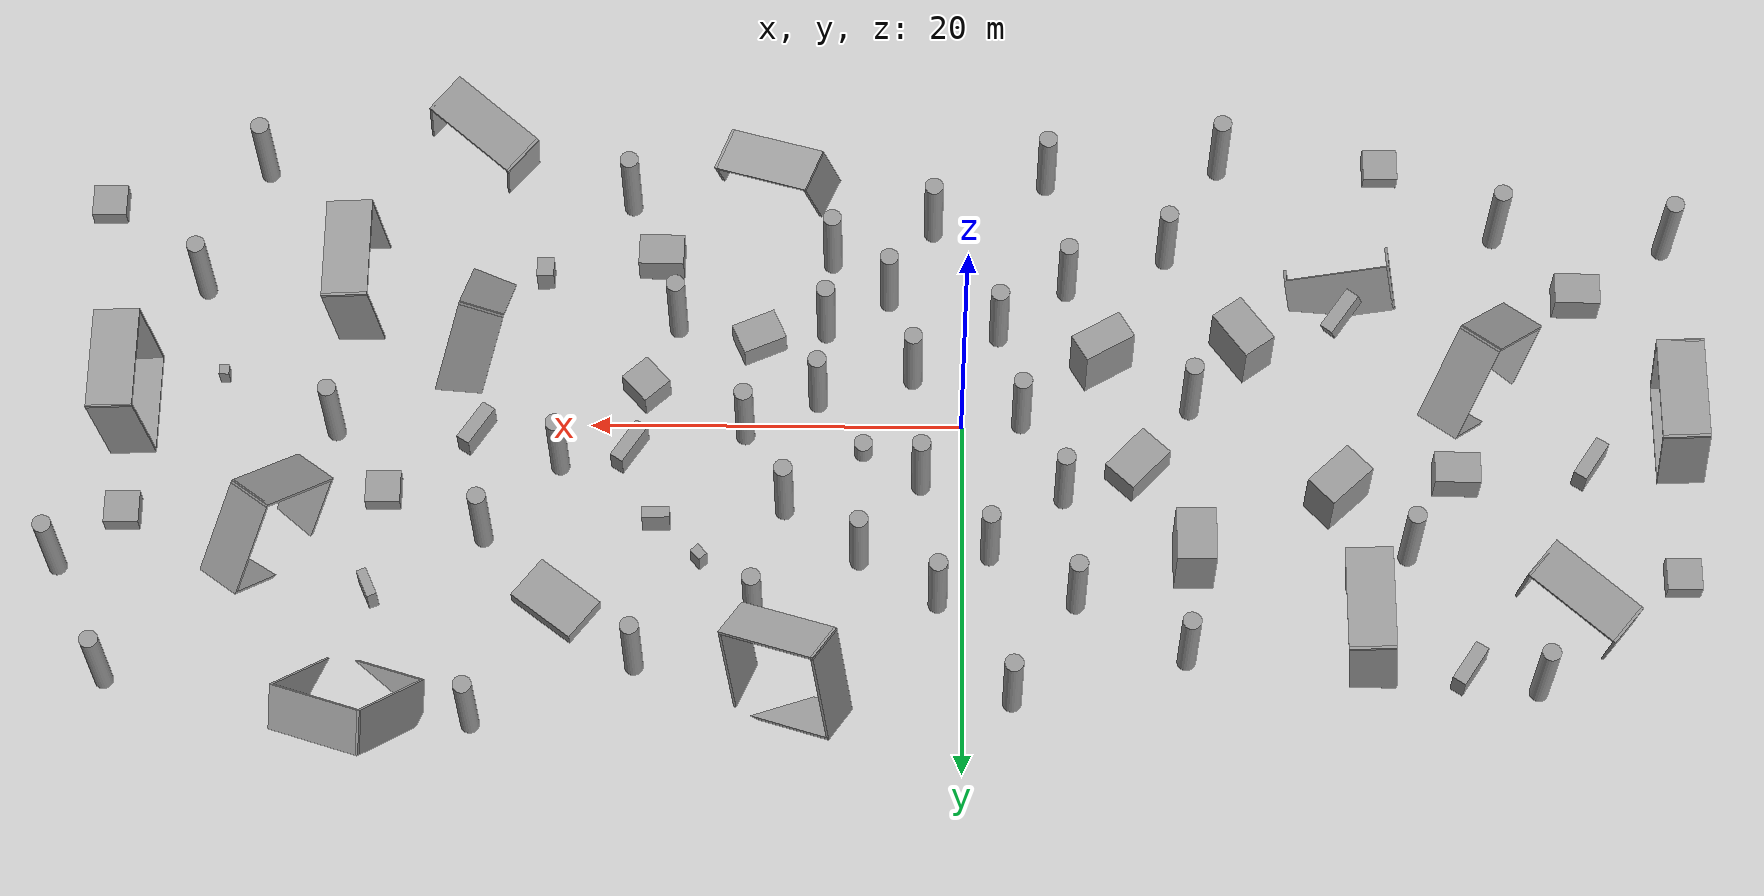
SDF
<sdf version="1.6">
 <world name="default">
  <light name="sun" type="directional">
   <pose>0 0 10 0 -0 0</pose>
   <diffuse>0.8 0.8 0.8 1</diffuse>
   <specular>0.2 0.2 0.2 1</specular>
   <attenuation>
    <range>1000</range>
    <constant>0.9</constant>
    <linear>0.01</linear>
    <quadratic>0.001</quadratic>
   </attenuation>
   <direction>-0.5 0.1 -0.9</direction>
  </light>
  <model name="ground_plane">
   <static>1</static>
   <link name="link">
    <collision name="collision">
     <geometry><plane><normal>0 0 1</normal><size>100 100</size></plane></geometry>
     <surface><friction><ode><mu>100</mu><mu2>50</mu2></ode></friction></surface>
    </collision>
    <visual name="visual">
     <cast_shadows>0</cast_shadows>
     <geometry><plane><normal>0 0 1</normal><size>100 100</size></plane></geometry>
     <material>
      <script><uri>file://media/materials/scripts/gazebo.material</uri><name>Gazebo/Grey</name></script>
     </material>
    </visual>
   </link>
  </model>
  <gravity>0 0 -9.8</gravity>
  <magnetic_field>6e-06 2.3e-05 -4.2e-05</magnetic_field>
  <atmosphere type="adiabatic"/>
  <physics name="default_physics" default="0" type="ode">
   <max_step_size>0.001</max_step_size>
   <real_time_factor>1</real_time_factor>
   <real_time_update_rate>1000</real_time_update_rate>
  </physics>
  <scene><ambient>0.4 0.4 0.4 1</ambient><background>0.7 0.7 0.7 1</background><shadows>1</shadows></scene>
  <audio><device>default</device></audio>
  <spherical_coordinates>
   <surface_model>EARTH_WGS84</surface_model>
   <latitude_deg>0</latitude_deg>
   <longitude_deg>0</longitude_deg>
   <elevation>0</elevation>
   <heading_deg>0</heading_deg>
  </spherical_coordinates>
  <model name="unit_cylinder">
   <pose>5.3177 1.52841 0.66176 0 -0 0.001729</pose>
   <link name="link">
    <inertial>
     <mass>1</mass>
     <inertia><ixx>0.145833</ixx><ixy>0</ixy><ixz>0</ixz><iyy>0.145833</iyy><iyz>0</iyz><izz>0.125</izz></inertia>
    </inertial>
    <collision name="collision">
     <geometry><cylinder><radius>0.5</radius><length>1.32353</length></cylinder></geometry>
    </collision>
    <visual name="visual">
     <geometry><cylinder><radius>0.5</radius><length>1.32353</length></cylinder></geometry>
     <material>
      <script><name>Gazebo/Grey</name><uri>file://media/materials/scripts/gazebo.material</uri></script>
     </material>
    </visual>
   </link>
  </model>
  <model name="unit_cylinder_clone">
   <pose>2.68095 -2.80478 2.75253 0 -0 0.003087</pose>
   <link name="link">
    <inertial>
     <mass>1</mass>
     <inertia><ixx>0.145833</ixx><ixy>0</ixy><ixz>0</ixz><iyy>0.145833</iyy><iyz>0</iyz><izz>0.125</izz></inertia>
    </inertial>
    <collision name="collision">
     <geometry><cylinder><radius>0.5</radius><length>5.50507</length></cylinder></geometry>
    </collision>
    <visual name="visual">
     <geometry><cylinder><radius>0.5</radius><length>5.50507</length></cylinder></geometry>
     <material>
      <script><name>Gazebo/Grey</name><uri>file://media/materials/scripts/gazebo.material</uri></script>
     </material>
    </visual>
   </link>
  </model>
  <model name="unit_cylinder_clone_0">
   <pose>2.22785 3.50849 2.75253 0 -0 0.003117</pose>
   <link name="link">
    <inertial>
     <mass>1</mass>
     <inertia><ixx>0.145833</ixx><ixy>0</ixy><ixz>0</ixz><iyy>0.145833</iyy><iyz>0</iyz><izz>0.125</izz></inertia>
    </inertial>
    <collision name="collision">
     <geometry><cylinder><radius>0.5</radius><length>5.50507</length></cylinder></geometry>
    </collision>
    <visual name="visual">
     <geometry><cylinder><radius>0.5</radius><length>5.50507</length></cylinder></geometry>
     <material>
      <script><name>Gazebo/Grey</name><uri>file://media/materials/scripts/gazebo.material</uri></script>
     </material>
    </visual>
   </link>
  </model>
  <model name="unit_cylinder_clone_1">
   <pose>7.38499 -5.59562 2.75253 0 -0 0.002942</pose>
   <link name="link">
    <inertial>
     <mass>1</mass>
     <inertia><ixx>0.145833</ixx><ixy>0</ixy><ixz>0</ixz><iyy>0.145833</iyy><iyz>0</iyz><izz>0.125</izz></inertia>
    </inertial>
    <collision name="collision">
     <geometry><cylinder><radius>0.5</radius><length>5.50507</length></cylinder></geometry>
    </collision>
    <visual name="visual">
     <geometry><cylinder><radius>0.5</radius><length>5.50507</length></cylinder></geometry>
     <material>
      <script><name>Gazebo/Grey</name><uri>file://media/materials/scripts/gazebo.material</uri></script>
     </material>
    </visual>
   </link>
  </model>
  <model name="unit_cylinder_clone_2">
   <pose>9.49418 5.00022 2.75253 0 -0 0.003097</pose>
   <link name="link">
    <inertial>
     <mass>1</mass>
     <inertia><ixx>0.145833</ixx><ixy>0</ixy><ixz>0</ixz><iyy>0.145833</iyy><iyz>0</iyz><izz>0.125</izz></inertia>
    </inertial>
    <collision name="collision">
     <geometry><cylinder><radius>0.5</radius><length>5.50507</length></cylinder></geometry>
    </collision>
    <visual name="visual">
     <geometry><cylinder><radius>0.5</radius><length>5.50507</length></cylinder></geometry>
     <material>
      <script><name>Gazebo/Grey</name><uri>file://media/materials/scripts/gazebo.material</uri></script>
     </material>
    </visual>
   </link>
  </model>
  <model name="unit_cylinder_clone_3">
   <pose>7.77893 -1.37954 2.75253 0 -0 0.003339</pose>
   <link name="link">
    <inertial>
     <mass>1</mass>
     <inertia><ixx>0.145833</ixx><ixy>0</ixy><ixz>0</ixz><iyy>0.145833</iyy><iyz>0</iyz><izz>0.125</izz></inertia>
    </inertial>
    <collision name="collision">
     <geometry><cylinder><radius>0.5</radius><length>5.50507</length></cylinder></geometry>
    </collision>
    <visual name="visual">
     <geometry><cylinder><radius>0.5</radius><length>5.50507</length></cylinder></geometry>
     <material>
      <script><name>Gazebo/Grey</name><uri>file://media/materials/scripts/gazebo.material</uri></script>
     </material>
    </visual>
   </link>
  </model>
  <model name="unit_cylinder_clone_4">
   <pose>3.98747 -7.5391 2.75253 0 -0 0.003351</pose>
   <link name="link">
    <inertial>
     <mass>1</mass>
     <inertia><ixx>0.145833</ixx><ixy>0</ixy><ixz>0</ixz><iyy>0.145833</iyy><iyz>0</iyz><izz>0.125</izz></inertia>
    </inertial>
    <collision name="collision">
     <geometry><cylinder><radius>0.5</radius><length>5.50507</length></cylinder></geometry>
    </collision>
    <visual name="visual">
     <geometry><cylinder><radius>0.5</radius><length>5.50507</length></cylinder></geometry>
     <material>
      <script><name>Gazebo/Grey</name><uri>file://media/materials/scripts/gazebo.material</uri></script>
     </material>
    </visual>
   </link>
  </model>
  <model name="unit_cylinder_clone_5">
   <pose>5.48239 7.91912 2.75253 0 -0 0.00293</pose>
   <link name="link">
    <inertial>
     <mass>1</mass>
     <inertia><ixx>0.145833</ixx><ixy>0</ixy><ixz>0</ixz><iyy>0.145833</iyy><iyz>0</iyz><izz>0.125</izz></inertia>
    </inertial>
    <collision name="collision">
     <geometry><cylinder><radius>0.5</radius><length>5.50507</length></cylinder></geometry>
    </collision>
    <visual name="visual">
     <geometry><cylinder><radius>0.5</radius><length>5.50507</length></cylinder></geometry>
     <material>
      <script><name>Gazebo/Grey</name><uri>file://media/materials/scripts/gazebo.material</uri></script>
     </material>
    </visual>
   </link>
  </model>
  <model name="unit_cylinder_clone_6">
   <pose>7.07457 -9.88001 2.75253 0 -0 0.00313</pose>
   <link name="link">
    <inertial>
     <mass>1</mass>
     <inertia><ixx>0.145833</ixx><ixy>0</ixy><ixz>0</ixz><iyy>0.145833</iyy><iyz>0</iyz><izz>0.125</izz></inertia>
    </inertial>
    <collision name="collision">
     <geometry><cylinder><radius>0.5</radius><length>5.50507</length></cylinder></geometry>
    </collision>
    <visual name="visual">
     <geometry><cylinder><radius>0.5</radius><length>5.50507</length></cylinder></geometry>
     <material>
      <script><name>Gazebo/Grey</name><uri>file://media/materials/scripts/gazebo.material</uri></script>
     </material>
    </visual>
   </link>
  </model>
  <model name="unit_cylinder_clone_7">
   <pose>11.6646 0.575183 2.75253 0 -0 0.003084</pose>
   <link name="link">
    <inertial>
     <mass>1</mass>
     <inertia><ixx>0.145833</ixx><ixy>0</ixy><ixz>0</ixz><iyy>0.145833</iyy><iyz>0</iyz><izz>0.125</izz></inertia>
    </inertial>
    <collision name="collision">
     <geometry><cylinder><radius>0.5</radius><length>5.50507</length></cylinder></geometry>
    </collision>
    <visual name="visual">
     <geometry><cylinder><radius>0.5</radius><length>5.50507</length></cylinder></geometry>
     <material>
      <script><name>Gazebo/Grey</name><uri>file://media/materials/scripts/gazebo.material</uri></script>
     </material>
    </visual>
   </link>
  </model>
  <model name="unit_cylinder_clone_8">
   <pose>11.0394 11.2508 2.75253 0 -0 0.003015</pose>
   <link name="link">
    <inertial>
     <mass>1</mass>
     <inertia><ixx>0.145833</ixx><ixy>0</ixy><ixz>0</ixz><iyy>0.145833</iyy><iyz>0</iyz><izz>0.125</izz></inertia>
    </inertial>
    <collision name="collision">
     <geometry><cylinder><radius>0.5</radius><length>5.50507</length></cylinder></geometry>
    </collision>
    <visual name="visual">
     <geometry><cylinder><radius>0.5</radius><length>5.50507</length></cylinder></geometry>
     <material>
      <script><name>Gazebo/Grey</name><uri>file://media/materials/scripts/gazebo.material</uri></script>
     </material>
    </visual>
   </link>
  </model>
  <model name="unit_cylinder_clone_9">
   <pose>1.3246 10.3757 2.75253 0 -0 0.003195</pose>
   <link name="link">
    <inertial>
     <mass>1</mass>
     <inertia><ixx>0.145833</ixx><ixy>0</ixy><ixz>0</ixz><iyy>0.145833</iyy><iyz>0</iyz><izz>0.125</izz></inertia>
    </inertial>
    <collision name="collision">
     <geometry><cylinder><radius>0.5</radius><length>5.50507</length></cylinder></geometry>
    </collision>
    <visual name="visual">
     <geometry><cylinder><radius>0.5</radius><length>5.50507</length></cylinder></geometry>
     <material>
      <script><name>Gazebo/Grey</name><uri>file://media/materials/scripts/gazebo.material</uri></script>
     </material>
    </visual>
   </link>
  </model>
  <model name="unit_cylinder_clone_12">
   <pose>15.4134 -5.85664 2.75253 0 -0 0.003344</pose>
   <link name="link">
    <inertial>
     <mass>1</mass>
     <inertia><ixx>0.145833</ixx><ixy>0</ixy><ixz>0</ixz><iyy>0.145833</iyy><iyz>0</iyz><izz>0.125</izz></inertia>
    </inertial>
    <collision name="collision">
     <geometry><cylinder><radius>0.5</radius><length>5.50507</length></cylinder></geometry>
    </collision>
    <visual name="visual">
     <geometry><cylinder><radius>0.5</radius><length>5.50507</length></cylinder></geometry>
     <material>
      <script><name>Gazebo/Grey</name><uri>file://media/materials/scripts/gazebo.material</uri></script>
     </material>
    </visual>
   </link>
  </model>
  <model name="unit_box">
   <pose>13.9889 7.99619 0.672427 -5e-06 5e-06 0.739095</pose>
   <link name="link">
    <inertial>
     <mass>1</mass>
     <inertia>
      <ixx>0.166667</ixx>
      <ixy>0</ixy>
      <ixz>0</ixz>
      <iyy>0.166667</iyy>
      <iyz>0</iyz>
      <izz>0.166667</izz>
     </inertia>
    </inertial>
    <collision name="collision"><geometry><box><size>0.564982 0.726007 1.34486</size></box></geometry></collision>
    <visual name="visual">
     <geometry><box><size>0.564982 0.726007 1.34486</size></box></geometry>
     <material>
      <script><name>Gazebo/Grey</name><uri>file://media/materials/scripts/gazebo.material</uri></script>
     </material>
    </visual>
   </link>
  </model>
  <model name="unit_box_clone">
   <pose>11 -5.00015 0.78823 -4e-06 -0 -1.15764</pose>
   <link name="link">
    <inertial>
     <mass>1</mass>
     <inertia>
      <ixx>0.166667</ixx>
      <ixy>0</ixy>
      <ixz>0</ixz>
      <iyy>0.166667</iyy>
      <iyz>0</iyz>
      <izz>0.166667</izz>
     </inertia>
    </inertial>
    <collision name="collision"><geometry><box><size>1.76997 2.44518 1.57647</size></box></geometry></collision>
    <visual name="visual">
     <geometry><box><size>1.76997 2.44518 1.57647</size></box></geometry>
     <material>
      <script><name>Gazebo/Grey</name><uri>file://media/materials/scripts/gazebo.material</uri></script>
     </material>
    </visual>
   </link>
  </model>
  <model name="unit_box_clone_0">
   <pose>17.0327 -2.04325 0.841035 0 -5e-06 0.733102</pose>
   <link name="link">
    <inertial>
     <mass>1</mass>
     <inertia>
      <ixx>0.166667</ixx>
      <ixy>0</ixy>
      <ixz>0</ixz>
      <iyy>0.166667</iyy>
      <iyz>0</iyz>
      <izz>0.166667</izz>
     </inertia>
    </inertial>
    <collision name="collision"><geometry><box><size>1.76997 1.92154 1.68208</size></box></geometry></collision>
    <visual name="visual">
     <geometry><box><size>1.76997 1.92154 1.68208</size></box></geometry>
     <material>
      <script><name>Gazebo/Grey</name><uri>file://media/materials/scripts/gazebo.material</uri></script>
     </material>
    </visual>
   </link>
  </model>
  <model name="unit_box_clone_1">
   <pose>16.3984 -9.84099 0.926301 0 5e-06 1.55039</pose>
   <link name="link">
    <inertial>
     <mass>1</mass>
     <inertia>
      <ixx>0.166667</ixx>
      <ixy>0</ixy>
      <ixz>0</ixz>
      <iyy>0.166667</iyy>
      <iyz>0</iyz>
      <izz>0.166667</izz>
     </inertia>
    </inertial>
    <collision name="collision"><geometry><box><size>1.76997 2.44518 1.85261</size></box></geometry></collision>
    <visual name="visual">
     <geometry><box><size>1.76997 2.44518 1.85261</size></box></geometry>
     <material>
      <script><name>Gazebo/Grey</name><uri>file://media/materials/scripts/gazebo.material</uri></script>
     </material>
    </visual>
   </link>
  </model>
  <model name="unit_box_clone_0_clone">
   <pose>21.504 10.512 0.43037 -1e-06 -1.57079 -0.657494</pose>
   <link name="link">
    <inertial>
     <mass>1</mass>
     <inertia>
      <ixx>0.166667</ixx>
      <ixy>0</ixy>
      <ixz>0</ixz>
      <iyy>0.166667</iyy>
      <iyz>0</iyz>
      <izz>0.166667</izz>
     </inertia>
    </inertial>
    <collision name="collision"><geometry><box><size>0.860775 2.57296 3.98743</size></box></geometry></collision>
    <visual name="visual">
     <geometry><box><size>0.860775 2.57296 3.98743</size></box></geometry>
     <material>
      <script><name>Gazebo/Grey</name><uri>file://media/materials/scripts/gazebo.material</uri></script>
     </material>
    </visual>
   </link>
  </model>
  <model name="unit_box_0">
   <pose>16.3175 5.84891 0.859724 0 -0 0.022299</pose>
   <link name="link">
    <inertial>
     <mass>1</mass>
     <inertia>
      <ixx>0.166667</ixx>
      <ixy>0</ixy>
      <ixz>0</ixz>
      <iyy>0.166667</iyy>
      <iyz>0</iyz>
      <izz>0.166667</izz>
     </inertia>
    </inertial>
    <collision name="collision"><geometry><box><size>1.47389 0.631413 1.71945</size></box></geometry></collision>
    <visual name="visual">
     <geometry><box><size>1.47389 0.631413 1.71945</size></box></geometry>
     <material>
      <script><name>Gazebo/Grey</name><uri>file://media/materials/scripts/gazebo.material</uri></script>
     </material>
    </visual>
   </link>
  </model>
  <model name="unit_box_clone_clone">
   <pose>26.0951 0.595663 0.788235 -0 -0 -0.573</pose>
   <link name="link">
    <inertial>
     <mass>1</mass>
     <inertia>
      <ixx>0.166667</ixx>
      <ixy>0</ixy>
      <ixz>0</ixz>
      <iyy>0.166667</iyy>
      <iyz>0</iyz>
      <izz>0.166667</izz>
     </inertia>
    </inertial>
    <collision name="collision"><geometry><box><size>0.770315 2.44518 1.57647</size></box></geometry></collision>
    <visual name="visual">
     <geometry><box><size>0.770315 2.44518 1.57647</size></box></geometry>
     <material>
      <script><name>Gazebo/Grey</name><uri>file://media/materials/scripts/gazebo.material</uri></script>
     </material>
    </visual>
   </link>
  </model>
  <model name="unit_box_clone_clone_0">
   <pose>22.7246 -8.85657 0.788235 0 -0 0.015585</pose>
   <link name="link">
    <inertial>
     <mass>1</mass>
     <inertia>
      <ixx>0.166667</ixx>
      <ixy>0</ixy>
      <ixz>0</ixz>
      <iyy>0.166667</iyy>
      <iyz>0</iyz>
      <izz>0.166667</izz>
     </inertia>
    </inertial>
    <collision name="collision"><geometry><box><size>0.926366 1.10204 1.57647</size></box></geometry></collision>
    <visual name="visual">
     <geometry><box><size>0.926366 1.10204 1.57647</size></box></geometry>
     <material>
      <script><name>Gazebo/Grey</name><uri>file://media/materials/scripts/gazebo.material</uri></script>
     </material>
    </visual>
   </link>
  </model>
  <model name="unit_box_clone_clone_1">
   <pose>31.4555 9.98516 0.788231 5e-06 -0 -2.72809</pose>
   <link name="link">
    <inertial>
     <mass>1</mass>
     <inertia>
      <ixx>0.166667</ixx>
      <ixy>0</ixy>
      <ixz>0</ixz>
      <iyy>0.166667</iyy>
      <iyz>0</iyz>
      <izz>0.166667</izz>
     </inertia>
    </inertial>
    <collision name="collision"><geometry><box><size>0.539862 1.60938 1.57647</size></box></geometry></collision>
    <visual name="visual">
     <geometry><box><size>0.539862 1.60938 1.57647</size></box></geometry>
     <material>
      <script><name>Gazebo/Grey</name><uri>file://media/materials/scripts/gazebo.material</uri></script>
     </material>
    </visual>
   </link>
  </model>
  <model name="unit_cylinder_clone_7_clone_0">
   <pose>25.5032 6.72847 2.75253 0 -0 0.003087</pose>
   <link name="link">
    <inertial>
     <mass>1</mass>
     <inertia><ixx>0.145833</ixx><ixy>0</ixy><ixz>0</ixz><iyy>0.145833</iyy><iyz>0</iyz><izz>0.125</izz></inertia>
    </inertial>
    <collision name="collision">
     <geometry><cylinder><radius>0.5</radius><length>5.50507</length></cylinder></geometry>
    </collision>
    <visual name="visual">
     <geometry><cylinder><radius>0.5</radius><length>5.50507</length></cylinder></geometry>
     <material>
      <script><name>Gazebo/Grey</name><uri>file://media/materials/scripts/gazebo.material</uri></script>
     </material>
    </visual>
   </link>
  </model>
  <model name="unit_cylinder_clone_7_clone_1">
   <pose>21.5647 2.44803 2.75253 0 -0 0.002969</pose>
   <link name="link">
    <inertial>
     <mass>1</mass>
     <inertia><ixx>0.145833</ixx><ixy>0</ixy><ixz>0</ixz><iyy>0.145833</iyy><iyz>0</iyz><izz>0.125</izz></inertia>
    </inertial>
    <collision name="collision">
     <geometry><cylinder><radius>0.5</radius><length>5.50507</length></cylinder></geometry>
    </collision>
    <visual name="visual">
     <geometry><cylinder><radius>0.5</radius><length>5.50507</length></cylinder></geometry>
     <material>
      <script><name>Gazebo/Grey</name><uri>file://media/materials/scripts/gazebo.material</uri></script>
     </material>
    </visual>
   </link>
  </model>
  <model name="unit_cylinder_clone_7_clone_2">
   <pose>17.2802 14.0465 2.75253 0 -0 0.002939</pose>
   <link name="link">
    <inertial>
     <mass>1</mass>
     <inertia><ixx>0.145833</ixx><ixy>0</ixy><ixz>0</ixz><iyy>0.145833</iyy><iyz>0</iyz><izz>0.125</izz></inertia>
    </inertial>
    <collision name="collision">
     <geometry><cylinder><radius>0.5</radius><length>5.50507</length></cylinder></geometry>
    </collision>
    <visual name="visual">
     <geometry><cylinder><radius>0.5</radius><length>5.50507</length></cylinder></geometry>
     <material>
      <script><name>Gazebo/Grey</name><uri>file://media/materials/scripts/gazebo.material</uri></script>
     </material>
    </visual>
   </link>
  </model>
  <model name="unit_cylinder_clone_7_clone_3">
   <pose>18.1064 -13.3672 2.75253 0 -0 0.003012</pose>
   <link name="link">
    <inertial>
     <mass>1</mass>
     <inertia><ixx>0.145833</ixx><ixy>0</ixy><ixz>0</ixz><iyy>0.145833</iyy><iyz>0</iyz><izz>0.125</izz></inertia>
    </inertial>
    <collision name="collision">
     <geometry><cylinder><radius>0.5</radius><length>5.50507</length></cylinder></geometry>
    </collision>
    <visual name="visual">
     <geometry><cylinder><radius>0.5</radius><length>5.50507</length></cylinder></geometry>
     <material>
      <script><name>Gazebo/Grey</name><uri>file://media/materials/scripts/gazebo.material</uri></script>
     </material>
    </visual>
   </link>
  </model>
  <model name="vRoom_clone_3_clone_clone_9">
   <link name="Wall_0">
    <pose>-2.8 -0 -1e-06 -0 -0 -1.5708</pose>
    <velocity_decay><linear>0</linear><angular>0</angular></velocity_decay>
    <visual name="Wall_0_Visual">
     <pose>0 0 1.25 0 -0 0</pose>
     <geometry><box><size>5.75 0.15 2.5</size></box></geometry>
     <material>
      <script><uri>file://media/materials/scripts/gazebo.material</uri><name>Gazebo/Grey</name></script>
      <ambient>1 1 1 1</ambient>
     </material>
    </visual>
    <collision name="Wall_0_Collision">
     <pose>0 0 1.25 0 -0 0</pose>
     <geometry><box><size>5.75 0.15 2.5</size></box></geometry>
     <surface>
      <friction>
       <ode><mu>1</mu><mu2>1</mu2><fdir1>0 0 0</fdir1><slip1>0</slip1><slip2>0</slip2></ode>
       <torsional>
        <coefficient>1</coefficient>
        <patch_radius>0</patch_radius>
        <surface_radius>0</surface_radius>
        <use_patch_radius>1</use_patch_radius>
        <ode><slip>0</slip></ode>
       </torsional>
      </friction>
      <bounce><restitution_coefficient>0</restitution_coefficient><threshold>1e+06</threshold></bounce>
      <contact>
       <collide_without_contact>0</collide_without_contact>
       <collide_without_contact_bitmask>1</collide_without_contact_bitmask>
       <collide_bitmask>1</collide_bitmask>
       <ode>
        <soft_cfm>0</soft_cfm>
        <soft_erp>0.2</soft_erp>
        <kp>1e+13</kp>
        <kd>1</kd>
        <max_vel>0.01</max_vel>
        <min_depth>0</min_depth>
       </ode>
       <bullet>
        <split_impulse>1</split_impulse>
        <split_impulse_penetration_threshold>-0.01</split_impulse_penetration_threshold>
        <soft_cfm>0</soft_cfm>
        <soft_erp>0.2</soft_erp>
        <kp>1e+13</kp>
        <kd>1</kd>
       </bullet>
      </contact>
     </surface>
    </collision>
   </link>
   <link name="Wall_1">
    <pose>2e-06 -2.8 2e-06 0 -0 0</pose>
    <velocity_decay><linear>0</linear><angular>0</angular></velocity_decay>
    <visual name="Wall_1_Visual">
     <pose>0 0 1.25 0 -0 0</pose>
     <geometry><box><size>5.75 0.15 2.5</size></box></geometry>
     <material>
      <script><uri>file://media/materials/scripts/gazebo.material</uri><name>Gazebo/Grey</name></script>
      <ambient>1 1 1 1</ambient>
     </material>
    </visual>
    <collision name="Wall_1_Collision">
     <pose>0 0 1.25 0 -0 0</pose>
     <geometry><box><size>5.75 0.15 2.5</size></box></geometry>
     <surface>
      <friction>
       <ode><mu>1</mu><mu2>1</mu2><fdir1>0 0 0</fdir1><slip1>0</slip1><slip2>0</slip2></ode>
       <torsional>
        <coefficient>1</coefficient>
        <patch_radius>0</patch_radius>
        <surface_radius>0</surface_radius>
        <use_patch_radius>1</use_patch_radius>
        <ode><slip>0</slip></ode>
       </torsional>
      </friction>
      <bounce><restitution_coefficient>0</restitution_coefficient><threshold>1e+06</threshold></bounce>
      <contact>
       <collide_without_contact>0</collide_without_contact>
       <collide_without_contact_bitmask>1</collide_without_contact_bitmask>
       <collide_bitmask>1</collide_bitmask>
       <ode>
        <soft_cfm>0</soft_cfm>
        <soft_erp>0.2</soft_erp>
        <kp>1e+13</kp>
        <kd>1</kd>
        <max_vel>0.01</max_vel>
        <min_depth>0</min_depth>
       </ode>
       <bullet>
        <split_impulse>1</split_impulse>
        <split_impulse_penetration_threshold>-0.01</split_impulse_penetration_threshold>
        <soft_cfm>0</soft_cfm>
        <soft_erp>0.2</soft_erp>
        <kp>1e+13</kp>
        <kd>1</kd>
       </bullet>
      </contact>
     </surface>
    </collision>
   </link>
   <link name="Wall_2">
    <pose>2.8 0 1e-06 0 -0 1.5708</pose>
    <velocity_decay><linear>0</linear><angular>0</angular></velocity_decay>
    <visual name="Wall_2_Visual">
     <pose>0 0 1.25 0 -0 0</pose>
     <geometry><box><size>5.75 0.15 2.5</size></box></geometry>
     <material>
      <script><uri>file://media/materials/scripts/gazebo.material</uri><name>Gazebo/Grey</name></script>
      <ambient>1 1 1 1</ambient>
     </material>
    </visual>
    <collision name="Wall_2_Collision">
     <pose>0 0 1.25 0 -0 0</pose>
     <geometry><box><size>5.75 0.15 2.5</size></box></geometry>
     <surface>
      <friction>
       <ode><mu>1</mu><mu2>1</mu2><fdir1>0 0 0</fdir1><slip1>0</slip1><slip2>0</slip2></ode>
       <torsional>
        <coefficient>1</coefficient>
        <patch_radius>0</patch_radius>
        <surface_radius>0</surface_radius>
        <use_patch_radius>1</use_patch_radius>
        <ode><slip>0</slip></ode>
       </torsional>
      </friction>
      <bounce><restitution_coefficient>0</restitution_coefficient><threshold>1e+06</threshold></bounce>
      <contact>
       <collide_without_contact>0</collide_without_contact>
       <collide_without_contact_bitmask>1</collide_without_contact_bitmask>
       <collide_bitmask>1</collide_bitmask>
       <ode>
        <soft_cfm>0</soft_cfm>
        <soft_erp>0.2</soft_erp>
        <kp>1e+13</kp>
        <kd>1</kd>
        <max_vel>0.01</max_vel>
        <min_depth>0</min_depth>
       </ode>
       <bullet>
        <split_impulse>1</split_impulse>
        <split_impulse_penetration_threshold>-0.01</split_impulse_penetration_threshold>
        <soft_cfm>0</soft_cfm>
        <soft_erp>0.2</soft_erp>
        <kp>1e+13</kp>
        <kd>1</kd>
       </bullet>
      </contact>
     </surface>
    </collision>
   </link>
   <link name="Wall_3">
    <pose>-2e-06 2.8 -2e-06 0 -0 3.14159</pose>
    <velocity_decay><linear>0</linear><angular>0</angular></velocity_decay>
    <visual name="Wall_3_Visual">
     <pose>0 0 1.25 0 -0 0</pose>
     <geometry><box><size>5.75 0.15 2.5</size></box></geometry>
     <material>
      <script><uri>file://media/materials/scripts/gazebo.material</uri><name>Gazebo/Grey</name></script>
      <ambient>1 1 1 1</ambient>
     </material>
    </visual>
    <collision name="Wall_3_Collision">
     <pose>0 0 1.25 0 -0 0</pose>
     <geometry><box><size>5.75 0.15 2.5</size></box></geometry>
     <surface>
      <friction>
       <ode><mu>1</mu><mu2>1</mu2><fdir1>0 0 0</fdir1><slip1>0</slip1><slip2>0</slip2></ode>
       <torsional>
        <coefficient>1</coefficient>
        <patch_radius>0</patch_radius>
        <surface_radius>0</surface_radius>
        <use_patch_radius>1</use_patch_radius>
        <ode><slip>0</slip></ode>
       </torsional>
      </friction>
      <bounce><restitution_coefficient>0</restitution_coefficient><threshold>1e+06</threshold></bounce>
      <contact>
       <collide_without_contact>0</collide_without_contact>
       <collide_without_contact_bitmask>1</collide_without_contact_bitmask>
       <collide_bitmask>1</collide_bitmask>
       <ode>
        <soft_cfm>0</soft_cfm>
        <soft_erp>0.2</soft_erp>
        <kp>1e+13</kp>
        <kd>1</kd>
        <max_vel>0.01</max_vel>
        <min_depth>0</min_depth>
       </ode>
       <bullet>
        <split_impulse>1</split_impulse>
        <split_impulse_penetration_threshold>-0.01</split_impulse_penetration_threshold>
        <soft_cfm>0</soft_cfm>
        <soft_erp>0.2</soft_erp>
        <kp>1e+13</kp>
        <kd>1</kd>
       </bullet>
      </contact>
     </surface>
    </collision>
   </link>
   <static>1</static>
   <pose>34.1246 -8.07118 2.16038 4e-06 -1.47998 -7e-06</pose>
  </model>
  <model name="vRoom_clone_3_clone_clone_9_clone">
   <link name="Wall_0">
    <pose>-2.8 -0 -1e-06 -0 -0 -1.5708</pose>
    <velocity_decay><linear>0</linear><angular>0</angular></velocity_decay>
    <visual name="Wall_0_Visual">
     <pose>0 0 1.25 0 -0 0</pose>
     <geometry><box><size>5.75 0.15 2.5</size></box></geometry>
     <material>
      <script><uri>file://media/materials/scripts/gazebo.material</uri><name>Gazebo/Grey</name></script>
      <ambient>1 1 1 1</ambient>
     </material>
    </visual>
    <collision name="Wall_0_Collision">
     <pose>0 0 1.25 0 -0 0</pose>
     <geometry><box><size>5.75 0.15 2.5</size></box></geometry>
     <surface>
      <friction>
       <ode><mu>1</mu><mu2>1</mu2><fdir1>0 0 0</fdir1><slip1>0</slip1><slip2>0</slip2></ode>
       <torsional>
        <coefficient>1</coefficient>
        <patch_radius>0</patch_radius>
        <surface_radius>0</surface_radius>
        <use_patch_radius>1</use_patch_radius>
        <ode><slip>0</slip></ode>
       </torsional>
      </friction>
      <bounce><restitution_coefficient>0</restitution_coefficient><threshold>1e+06</threshold></bounce>
      <contact>
       <collide_without_contact>0</collide_without_contact>
       <collide_without_contact_bitmask>1</collide_without_contact_bitmask>
       <collide_bitmask>1</collide_bitmask>
       <ode>
        <soft_cfm>0</soft_cfm>
        <soft_erp>0.2</soft_erp>
        <kp>1e+13</kp>
        <kd>1</kd>
        <max_vel>0.01</max_vel>
        <min_depth>0</min_depth>
       </ode>
       <bullet>
        <split_impulse>1</split_impulse>
        <split_impulse_penetration_threshold>-0.01</split_impulse_penetration_threshold>
        <soft_cfm>0</soft_cfm>
        <soft_erp>0.2</soft_erp>
        <kp>1e+13</kp>
        <kd>1</kd>
       </bullet>
      </contact>
     </surface>
    </collision>
   </link>
   <link name="Wall_1">
    <pose>2e-06 -2.8 2e-06 0 -0 0</pose>
    <velocity_decay><linear>0</linear><angular>0</angular></velocity_decay>
    <visual name="Wall_1_Visual">
     <pose>0 0 1.25 0 -0 0</pose>
     <geometry><box><size>5.75 0.15 2.5</size></box></geometry>
     <material>
      <script><uri>file://media/materials/scripts/gazebo.material</uri><name>Gazebo/Grey</name></script>
      <ambient>1 1 1 1</ambient>
     </material>
    </visual>
    <collision name="Wall_1_Collision">
     <pose>0 0 1.25 0 -0 0</pose>
     <geometry><box><size>5.75 0.15 2.5</size></box></geometry>
     <surface>
      <friction>
       <ode><mu>1</mu><mu2>1</mu2><fdir1>0 0 0</fdir1><slip1>0</slip1><slip2>0</slip2></ode>
       <torsional>
        <coefficient>1</coefficient>
        <patch_radius>0</patch_radius>
        <surface_radius>0</surface_radius>
        <use_patch_radius>1</use_patch_radius>
        <ode><slip>0</slip></ode>
       </torsional>
      </friction>
      <bounce><restitution_coefficient>0</restitution_coefficient><threshold>1e+06</threshold></bounce>
      <contact>
       <collide_without_contact>0</collide_without_contact>
       <collide_without_contact_bitmask>1</collide_without_contact_bitmask>
       <collide_bitmask>1</collide_bitmask>
       <ode>
        <soft_cfm>0</soft_cfm>
        <soft_erp>0.2</soft_erp>
        <kp>1e+13</kp>
        <kd>1</kd>
        <max_vel>0.01</max_vel>
        <min_depth>0</min_depth>
       </ode>
       <bullet>
        <split_impulse>1</split_impulse>
        <split_impulse_penetration_threshold>-0.01</split_impulse_penetration_threshold>
        <soft_cfm>0</soft_cfm>
        <soft_erp>0.2</soft_erp>
        <kp>1e+13</kp>
        <kd>1</kd>
       </bullet>
      </contact>
     </surface>
    </collision>
   </link>
   <link name="Wall_2">
    <pose>2.8 0 1e-06 0 -0 1.5708</pose>
    <velocity_decay><linear>0</linear><angular>0</angular></velocity_decay>
    <visual name="Wall_2_Visual">
     <pose>0 0 1.25 0 -0 0</pose>
     <geometry><box><size>5.75 0.15 2.5</size></box></geometry>
     <material>
      <script><uri>file://media/materials/scripts/gazebo.material</uri><name>Gazebo/Grey</name></script>
      <ambient>1 1 1 1</ambient>
     </material>
    </visual>
    <collision name="Wall_2_Collision">
     <pose>0 0 1.25 0 -0 0</pose>
     <geometry><box><size>5.75 0.15 2.5</size></box></geometry>
     <surface>
      <friction>
       <ode><mu>1</mu><mu2>1</mu2><fdir1>0 0 0</fdir1><slip1>0</slip1><slip2>0</slip2></ode>
       <torsional>
        <coefficient>1</coefficient>
        <patch_radius>0</patch_radius>
        <surface_radius>0</surface_radius>
        <use_patch_radius>1</use_patch_radius>
        <ode><slip>0</slip></ode>
       </torsional>
      </friction>
      <bounce><restitution_coefficient>0</restitution_coefficient><threshold>1e+06</threshold></bounce>
      <contact>
       <collide_without_contact>0</collide_without_contact>
       <collide_without_contact_bitmask>1</collide_without_contact_bitmask>
       <collide_bitmask>1</collide_bitmask>
       <ode>
        <soft_cfm>0</soft_cfm>
        <soft_erp>0.2</soft_erp>
        <kp>1e+13</kp>
        <kd>1</kd>
        <max_vel>0.01</max_vel>
        <min_depth>0</min_depth>
       </ode>
       <bullet>
        <split_impulse>1</split_impulse>
        <split_impulse_penetration_threshold>-0.01</split_impulse_penetration_threshold>
        <soft_cfm>0</soft_cfm>
        <soft_erp>0.2</soft_erp>
        <kp>1e+13</kp>
        <kd>1</kd>
       </bullet>
      </contact>
     </surface>
    </collision>
   </link>
   <link name="Wall_3">
    <pose>-2e-06 2.8 -2e-06 0 -0 3.14159</pose>
    <velocity_decay><linear>0</linear><angular>0</angular></velocity_decay>
    <visual name="Wall_3_Visual">
     <pose>0 0 1.25 0 -0 0</pose>
     <geometry><box><size>5.75 0.15 2.5</size></box></geometry>
     <material>
      <script><uri>file://media/materials/scripts/gazebo.material</uri><name>Gazebo/Grey</name></script>
      <ambient>1 1 1 1</ambient>
     </material>
    </visual>
    <collision name="Wall_3_Collision">
     <pose>0 0 1.25 0 -0 0</pose>
     <geometry><box><size>5.75 0.15 2.5</size></box></geometry>
     <surface>
      <friction>
       <ode><mu>1</mu><mu2>1</mu2><fdir1>0 0 0</fdir1><slip1>0</slip1><slip2>0</slip2></ode>
       <torsional>
        <coefficient>1</coefficient>
        <patch_radius>0</patch_radius>
        <surface_radius>0</surface_radius>
        <use_patch_radius>1</use_patch_radius>
        <ode><slip>0</slip></ode>
       </torsional>
      </friction>
      <bounce><restitution_coefficient>0</restitution_coefficient><threshold>1e+06</threshold></bounce>
      <contact>
       <collide_without_contact>0</collide_without_contact>
       <collide_without_contact_bitmask>1</collide_without_contact_bitmask>
       <collide_bitmask>1</collide_bitmask>
       <ode>
        <soft_cfm>0</soft_cfm>
        <soft_erp>0.2</soft_erp>
        <kp>1e+13</kp>
        <kd>1</kd>
        <max_vel>0.01</max_vel>
        <min_depth>0</min_depth>
       </ode>
       <bullet>
        <split_impulse>1</split_impulse>
        <split_impulse_penetration_threshold>-0.01</split_impulse_penetration_threshold>
        <soft_cfm>0</soft_cfm>
        <soft_erp>0.2</soft_erp>
        <kp>1e+13</kp>
        <kd>1</kd>
       </bullet>
      </contact>
     </surface>
    </collision>
   </link>
   <static>1</static>
   <pose>37.7929 6.19167 2.16038 1.45974 -0.860248 -2.1368</pose>
  </model>
  <model name="vRoom_clone_3_clone_clone_9_clone_0">
   <link name="Wall_0">
    <pose>-2.8 -0 -1e-06 -0 -0 -1.5708</pose>
    <velocity_decay><linear>0</linear><angular>0</angular></velocity_decay>
    <visual name="Wall_0_Visual">
     <pose>0 0 1.25 0 -0 0</pose>
     <geometry><box><size>5.75 0.15 2.5</size></box></geometry>
     <material>
      <script><uri>file://media/materials/scripts/gazebo.material</uri><name>Gazebo/Grey</name></script>
      <ambient>1 1 1 1</ambient>
     </material>
    </visual>
    <collision name="Wall_0_Collision">
     <pose>0 0 1.25 0 -0 0</pose>
     <geometry><box><size>5.75 0.15 2.5</size></box></geometry>
     <surface>
      <friction>
       <ode><mu>1</mu><mu2>1</mu2><fdir1>0 0 0</fdir1><slip1>0</slip1><slip2>0</slip2></ode>
       <torsional>
        <coefficient>1</coefficient>
        <patch_radius>0</patch_radius>
        <surface_radius>0</surface_radius>
        <use_patch_radius>1</use_patch_radius>
        <ode><slip>0</slip></ode>
       </torsional>
      </friction>
      <bounce><restitution_coefficient>0</restitution_coefficient><threshold>1e+06</threshold></bounce>
      <contact>
       <collide_without_contact>0</collide_without_contact>
       <collide_without_contact_bitmask>1</collide_without_contact_bitmask>
       <collide_bitmask>1</collide_bitmask>
       <ode>
        <soft_cfm>0</soft_cfm>
        <soft_erp>0.2</soft_erp>
        <kp>1e+13</kp>
        <kd>1</kd>
        <max_vel>0.01</max_vel>
        <min_depth>0</min_depth>
       </ode>
       <bullet>
        <split_impulse>1</split_impulse>
        <split_impulse_penetration_threshold>-0.01</split_impulse_penetration_threshold>
        <soft_cfm>0</soft_cfm>
        <soft_erp>0.2</soft_erp>
        <kp>1e+13</kp>
        <kd>1</kd>
       </bullet>
      </contact>
     </surface>
    </collision>
   </link>
   <link name="Wall_1">
    <pose>2e-06 -2.8 2e-06 0 -0 0</pose>
    <velocity_decay><linear>0</linear><angular>0</angular></velocity_decay>
    <visual name="Wall_1_Visual">
     <pose>0 0 1.25 0 -0 0</pose>
     <geometry><box><size>5.75 0.15 2.5</size></box></geometry>
     <material>
      <script><uri>file://media/materials/scripts/gazebo.material</uri><name>Gazebo/Grey</name></script>
      <ambient>1 1 1 1</ambient>
     </material>
    </visual>
    <collision name="Wall_1_Collision">
     <pose>0 0 1.25 0 -0 0</pose>
     <geometry><box><size>5.75 0.15 2.5</size></box></geometry>
     <surface>
      <friction>
       <ode><mu>1</mu><mu2>1</mu2><fdir1>0 0 0</fdir1><slip1>0</slip1><slip2>0</slip2></ode>
       <torsional>
        <coefficient>1</coefficient>
        <patch_radius>0</patch_radius>
        <surface_radius>0</surface_radius>
        <use_patch_radius>1</use_patch_radius>
        <ode><slip>0</slip></ode>
       </torsional>
      </friction>
      <bounce><restitution_coefficient>0</restitution_coefficient><threshold>1e+06</threshold></bounce>
      <contact>
       <collide_without_contact>0</collide_without_contact>
       <collide_without_contact_bitmask>1</collide_without_contact_bitmask>
       <collide_bitmask>1</collide_bitmask>
       <ode>
        <soft_cfm>0</soft_cfm>
        <soft_erp>0.2</soft_erp>
        <kp>1e+13</kp>
        <kd>1</kd>
        <max_vel>0.01</max_vel>
        <min_depth>0</min_depth>
       </ode>
       <bullet>
        <split_impulse>1</split_impulse>
        <split_impulse_penetration_threshold>-0.01</split_impulse_penetration_threshold>
        <soft_cfm>0</soft_cfm>
        <soft_erp>0.2</soft_erp>
        <kp>1e+13</kp>
        <kd>1</kd>
       </bullet>
      </contact>
     </surface>
    </collision>
   </link>
   <link name="Wall_2">
    <pose>2.8 0 1e-06 0 -0 1.5708</pose>
    <velocity_decay><linear>0</linear><angular>0</angular></velocity_decay>
    <visual name="Wall_2_Visual">
     <pose>0 0 1.25 0 -0 0</pose>
     <geometry><box><size>5.75 0.15 2.5</size></box></geometry>
     <material>
      <script><uri>file://media/materials/scripts/gazebo.material</uri><name>Gazebo/Grey</name></script>
      <ambient>1 1 1 1</ambient>
     </material>
    </visual>
    <collision name="Wall_2_Collision">
     <pose>0 0 1.25 0 -0 0</pose>
     <geometry><box><size>5.75 0.15 2.5</size></box></geometry>
     <surface>
      <friction>
       <ode><mu>1</mu><mu2>1</mu2><fdir1>0 0 0</fdir1><slip1>0</slip1><slip2>0</slip2></ode>
       <torsional>
        <coefficient>1</coefficient>
        <patch_radius>0</patch_radius>
        <surface_radius>0</surface_radius>
        <use_patch_radius>1</use_patch_radius>
        <ode><slip>0</slip></ode>
       </torsional>
      </friction>
      <bounce><restitution_coefficient>0</restitution_coefficient><threshold>1e+06</threshold></bounce>
      <contact>
       <collide_without_contact>0</collide_without_contact>
       <collide_without_contact_bitmask>1</collide_without_contact_bitmask>
       <collide_bitmask>1</collide_bitmask>
       <ode>
        <soft_cfm>0</soft_cfm>
        <soft_erp>0.2</soft_erp>
        <kp>1e+13</kp>
        <kd>1</kd>
        <max_vel>0.01</max_vel>
        <min_depth>0</min_depth>
       </ode>
       <bullet>
        <split_impulse>1</split_impulse>
        <split_impulse_penetration_threshold>-0.01</split_impulse_penetration_threshold>
        <soft_cfm>0</soft_cfm>
        <soft_erp>0.2</soft_erp>
        <kp>1e+13</kp>
        <kd>1</kd>
       </bullet>
      </contact>
     </surface>
    </collision>
   </link>
   <link name="Wall_3">
    <pose>-2e-06 2.8 -2e-06 0 -0 3.14159</pose>
    <velocity_decay><linear>0</linear><angular>0</angular></velocity_decay>
    <visual name="Wall_3_Visual">
     <pose>0 0 1.25 0 -0 0</pose>
     <geometry><box><size>5.75 0.15 2.5</size></box></geometry>
     <material>
      <script><uri>file://media/materials/scripts/gazebo.material</uri><name>Gazebo/Grey</name></script>
      <ambient>1 1 1 1</ambient>
     </material>
    </visual>
    <collision name="Wall_3_Collision">
     <pose>0 0 1.25 0 -0 0</pose>
     <geometry><box><size>5.75 0.15 2.5</size></box></geometry>
     <surface>
      <friction>
       <ode><mu>1</mu><mu2>1</mu2><fdir1>0 0 0</fdir1><slip1>0</slip1><slip2>0</slip2></ode>
       <torsional>
        <coefficient>1</coefficient>
        <patch_radius>0</patch_radius>
        <surface_radius>0</surface_radius>
        <use_patch_radius>1</use_patch_radius>
        <ode><slip>0</slip></ode>
       </torsional>
      </friction>
      <bounce><restitution_coefficient>0</restitution_coefficient><threshold>1e+06</threshold></bounce>
      <contact>
       <collide_without_contact>0</collide_without_contact>
       <collide_without_contact_bitmask>1</collide_without_contact_bitmask>
       <collide_bitmask>1</collide_bitmask>
       <ode>
        <soft_cfm>0</soft_cfm>
        <soft_erp>0.2</soft_erp>
        <kp>1e+13</kp>
        <kd>1</kd>
        <max_vel>0.01</max_vel>
        <min_depth>0</min_depth>
       </ode>
       <bullet>
        <split_impulse>1</split_impulse>
        <split_impulse_penetration_threshold>-0.01</split_impulse_penetration_threshold>
        <soft_cfm>0</soft_cfm>
        <soft_erp>0.2</soft_erp>
        <kp>1e+13</kp>
        <kd>1</kd>
       </bullet>
      </contact>
     </surface>
    </collision>
   </link>
   <static>1</static>
   <pose>27.2029 -16.0391 0.534522 -1.11103 -1.4406 1.99895</pose>
  </model>
  <model name="vRoom_clone_3_clone_clone_9_clone_clone">
   <link name="Wall_0">
    <pose>-2.8 -0 -1e-06 -0 -0 -1.5708</pose>
    <velocity_decay><linear>0</linear><angular>0</angular></velocity_decay>
    <visual name="Wall_0_Visual">
     <pose>0 0 1.25 0 -0 0</pose>
     <geometry><box><size>5.75 0.15 2.5</size></box></geometry>
     <material>
      <script><uri>file://media/materials/scripts/gazebo.material</uri><name>Gazebo/Grey</name></script>
      <ambient>1 1 1 1</ambient>
     </material>
    </visual>
    <collision name="Wall_0_Collision">
     <pose>0 0 1.25 0 -0 0</pose>
     <geometry><box><size>5.75 0.15 2.5</size></box></geometry>
     <surface>
      <friction>
       <ode><mu>1</mu><mu2>1</mu2><fdir1>0 0 0</fdir1><slip1>0</slip1><slip2>0</slip2></ode>
       <torsional>
        <coefficient>1</coefficient>
        <patch_radius>0</patch_radius>
        <surface_radius>0</surface_radius>
        <use_patch_radius>1</use_patch_radius>
        <ode><slip>0</slip></ode>
       </torsional>
      </friction>
      <bounce><restitution_coefficient>0</restitution_coefficient><threshold>1e+06</threshold></bounce>
      <contact>
       <collide_without_contact>0</collide_without_contact>
       <collide_without_contact_bitmask>1</collide_without_contact_bitmask>
       <collide_bitmask>1</collide_bitmask>
       <ode>
        <soft_cfm>0</soft_cfm>
        <soft_erp>0.2</soft_erp>
        <kp>1e+13</kp>
        <kd>1</kd>
        <max_vel>0.01</max_vel>
        <min_depth>0</min_depth>
       </ode>
       <bullet>
        <split_impulse>1</split_impulse>
        <split_impulse_penetration_threshold>-0.01</split_impulse_penetration_threshold>
        <soft_cfm>0</soft_cfm>
        <soft_erp>0.2</soft_erp>
        <kp>1e+13</kp>
        <kd>1</kd>
       </bullet>
      </contact>
     </surface>
    </collision>
   </link>
   <link name="Wall_1">
    <pose>2e-06 -2.8 2e-06 0 -0 0</pose>
    <velocity_decay><linear>0</linear><angular>0</angular></velocity_decay>
    <visual name="Wall_1_Visual">
     <pose>0 0 1.25 0 -0 0</pose>
     <geometry><box><size>5.75 0.15 2.5</size></box></geometry>
     <material>
      <script><uri>file://media/materials/scripts/gazebo.material</uri><name>Gazebo/Grey</name></script>
      <ambient>1 1 1 1</ambient>
     </material>
    </visual>
    <collision name="Wall_1_Collision">
     <pose>0 0 1.25 0 -0 0</pose>
     <geometry><box><size>5.75 0.15 2.5</size></box></geometry>
     <surface>
      <friction>
       <ode><mu>1</mu><mu2>1</mu2><fdir1>0 0 0</fdir1><slip1>0</slip1><slip2>0</slip2></ode>
       <torsional>
        <coefficient>1</coefficient>
        <patch_radius>0</patch_radius>
        <surface_radius>0</surface_radius>
        <use_patch_radius>1</use_patch_radius>
        <ode><slip>0</slip></ode>
       </torsional>
      </friction>
      <bounce><restitution_coefficient>0</restitution_coefficient><threshold>1e+06</threshold></bounce>
      <contact>
       <collide_without_contact>0</collide_without_contact>
       <collide_without_contact_bitmask>1</collide_without_contact_bitmask>
       <collide_bitmask>1</collide_bitmask>
       <ode>
        <soft_cfm>0</soft_cfm>
        <soft_erp>0.2</soft_erp>
        <kp>1e+13</kp>
        <kd>1</kd>
        <max_vel>0.01</max_vel>
        <min_depth>0</min_depth>
       </ode>
       <bullet>
        <split_impulse>1</split_impulse>
        <split_impulse_penetration_threshold>-0.01</split_impulse_penetration_threshold>
        <soft_cfm>0</soft_cfm>
        <soft_erp>0.2</soft_erp>
        <kp>1e+13</kp>
        <kd>1</kd>
       </bullet>
      </contact>
     </surface>
    </collision>
   </link>
   <link name="Wall_2">
    <pose>2.8 0 1e-06 0 -0 1.5708</pose>
    <velocity_decay><linear>0</linear><angular>0</angular></velocity_decay>
    <visual name="Wall_2_Visual">
     <pose>0 0 1.25 0 -0 0</pose>
     <geometry><box><size>5.75 0.15 2.5</size></box></geometry>
     <material>
      <script><uri>file://media/materials/scripts/gazebo.material</uri><name>Gazebo/Grey</name></script>
      <ambient>1 1 1 1</ambient>
     </material>
    </visual>
    <collision name="Wall_2_Collision">
     <pose>0 0 1.25 0 -0 0</pose>
     <geometry><box><size>5.75 0.15 2.5</size></box></geometry>
     <surface>
      <friction>
       <ode><mu>1</mu><mu2>1</mu2><fdir1>0 0 0</fdir1><slip1>0</slip1><slip2>0</slip2></ode>
       <torsional>
        <coefficient>1</coefficient>
        <patch_radius>0</patch_radius>
        <surface_radius>0</surface_radius>
        <use_patch_radius>1</use_patch_radius>
        <ode><slip>0</slip></ode>
       </torsional>
      </friction>
      <bounce><restitution_coefficient>0</restitution_coefficient><threshold>1e+06</threshold></bounce>
      <contact>
       <collide_without_contact>0</collide_without_contact>
       <collide_without_contact_bitmask>1</collide_without_contact_bitmask>
       <collide_bitmask>1</collide_bitmask>
       <ode>
        <soft_cfm>0</soft_cfm>
        <soft_erp>0.2</soft_erp>
        <kp>1e+13</kp>
        <kd>1</kd>
        <max_vel>0.01</max_vel>
        <min_depth>0</min_depth>
       </ode>
       <bullet>
        <split_impulse>1</split_impulse>
        <split_impulse_penetration_threshold>-0.01</split_impulse_penetration_threshold>
        <soft_cfm>0</soft_cfm>
        <soft_erp>0.2</soft_erp>
        <kp>1e+13</kp>
        <kd>1</kd>
       </bullet>
      </contact>
     </surface>
    </collision>
   </link>
   <link name="Wall_3">
    <pose>-2e-06 2.8 -2e-06 0 -0 3.14159</pose>
    <velocity_decay><linear>0</linear><angular>0</angular></velocity_decay>
    <visual name="Wall_3_Visual">
     <pose>0 0 1.25 0 -0 0</pose>
     <geometry><box><size>5.75 0.15 2.5</size></box></geometry>
     <material>
      <script><uri>file://media/materials/scripts/gazebo.material</uri><name>Gazebo/Grey</name></script>
      <ambient>1 1 1 1</ambient>
     </material>
    </visual>
    <collision name="Wall_3_Collision">
     <pose>0 0 1.25 0 -0 0</pose>
     <geometry><box><size>5.75 0.15 2.5</size></box></geometry>
     <surface>
      <friction>
       <ode><mu>1</mu><mu2>1</mu2><fdir1>0 0 0</fdir1><slip1>0</slip1><slip2>0</slip2></ode>
       <torsional>
        <coefficient>1</coefficient>
        <patch_radius>0</patch_radius>
        <surface_radius>0</surface_radius>
        <use_patch_radius>1</use_patch_radius>
        <ode><slip>0</slip></ode>
       </torsional>
      </friction>
      <bounce><restitution_coefficient>0</restitution_coefficient><threshold>1e+06</threshold></bounce>
      <contact>
       <collide_without_contact>0</collide_without_contact>
       <collide_without_contact_bitmask>1</collide_without_contact_bitmask>
       <collide_bitmask>1</collide_bitmask>
       <ode>
        <soft_cfm>0</soft_cfm>
        <soft_erp>0.2</soft_erp>
        <kp>1e+13</kp>
        <kd>1</kd>
        <max_vel>0.01</max_vel>
        <min_depth>0</min_depth>
       </ode>
       <bullet>
        <split_impulse>1</split_impulse>
        <split_impulse_penetration_threshold>-0.01</split_impulse_penetration_threshold>
        <soft_cfm>0</soft_cfm>
        <soft_erp>0.2</soft_erp>
        <kp>1e+13</kp>
        <kd>1</kd>
       </bullet>
      </contact>
     </surface>
    </collision>
   </link>
   <static>1</static>
   <pose>32.0507 15.9163 2.16037 2.38794 -0.326145 2.72159</pose>
  </model>
  <model name="vRoom_clone_3_clone_clone_9_clone_1">
   <link name="Wall_0">
    <pose>-2.8 -0 -1e-06 -0 -0 -1.5708</pose>
    <velocity_decay><linear>0</linear><angular>0</angular></velocity_decay>
    <visual name="Wall_0_Visual">
     <pose>0 0 1.25 0 -0 0</pose>
     <geometry><box><size>5.75 0.15 2.5</size></box></geometry>
     <material>
      <script><uri>file://media/materials/scripts/gazebo.material</uri><name>Gazebo/Grey</name></script>
      <ambient>1 1 1 1</ambient>
     </material>
    </visual>
    <collision name="Wall_0_Collision">
     <pose>0 0 1.25 0 -0 0</pose>
     <geometry><box><size>5.75 0.15 2.5</size></box></geometry>
     <surface>
      <friction>
       <ode><mu>1</mu><mu2>1</mu2><fdir1>0 0 0</fdir1><slip1>0</slip1><slip2>0</slip2></ode>
       <torsional>
        <coefficient>1</coefficient>
        <patch_radius>0</patch_radius>
        <surface_radius>0</surface_radius>
        <use_patch_radius>1</use_patch_radius>
        <ode><slip>0</slip></ode>
       </torsional>
      </friction>
      <bounce><restitution_coefficient>0</restitution_coefficient><threshold>1e+06</threshold></bounce>
      <contact>
       <collide_without_contact>0</collide_without_contact>
       <collide_without_contact_bitmask>1</collide_without_contact_bitmask>
       <collide_bitmask>1</collide_bitmask>
       <ode>
        <soft_cfm>0</soft_cfm>
        <soft_erp>0.2</soft_erp>
        <kp>1e+13</kp>
        <kd>1</kd>
        <max_vel>0.01</max_vel>
        <min_depth>0</min_depth>
       </ode>
       <bullet>
        <split_impulse>1</split_impulse>
        <split_impulse_penetration_threshold>-0.01</split_impulse_penetration_threshold>
        <soft_cfm>0</soft_cfm>
        <soft_erp>0.2</soft_erp>
        <kp>1e+13</kp>
        <kd>1</kd>
       </bullet>
      </contact>
     </surface>
    </collision>
   </link>
   <link name="Wall_1">
    <pose>2e-06 -2.8 2e-06 0 -0 0</pose>
    <velocity_decay><linear>0</linear><angular>0</angular></velocity_decay>
    <visual name="Wall_1_Visual">
     <pose>0 0 1.25 0 -0 0</pose>
     <geometry><box><size>5.75 0.15 2.5</size></box></geometry>
     <material>
      <script><uri>file://media/materials/scripts/gazebo.material</uri><name>Gazebo/Grey</name></script>
      <ambient>1 1 1 1</ambient>
     </material>
    </visual>
    <collision name="Wall_1_Collision">
     <pose>0 0 1.25 0 -0 0</pose>
     <geometry><box><size>5.75 0.15 2.5</size></box></geometry>
     <surface>
      <friction>
       <ode><mu>1</mu><mu2>1</mu2><fdir1>0 0 0</fdir1><slip1>0</slip1><slip2>0</slip2></ode>
       <torsional>
        <coefficient>1</coefficient>
        <patch_radius>0</patch_radius>
        <surface_radius>0</surface_radius>
        <use_patch_radius>1</use_patch_radius>
        <ode><slip>0</slip></ode>
       </torsional>
      </friction>
      <bounce><restitution_coefficient>0</restitution_coefficient><threshold>1e+06</threshold></bounce>
      <contact>
       <collide_without_contact>0</collide_without_contact>
       <collide_without_contact_bitmask>1</collide_without_contact_bitmask>
       <collide_bitmask>1</collide_bitmask>
       <ode>
        <soft_cfm>0</soft_cfm>
        <soft_erp>0.2</soft_erp>
        <kp>1e+13</kp>
        <kd>1</kd>
        <max_vel>0.01</max_vel>
        <min_depth>0</min_depth>
       </ode>
       <bullet>
        <split_impulse>1</split_impulse>
        <split_impulse_penetration_threshold>-0.01</split_impulse_penetration_threshold>
        <soft_cfm>0</soft_cfm>
        <soft_erp>0.2</soft_erp>
        <kp>1e+13</kp>
        <kd>1</kd>
       </bullet>
      </contact>
     </surface>
    </collision>
   </link>
   <link name="Wall_2">
    <pose>2.8 0 1e-06 0 -0 1.5708</pose>
    <velocity_decay><linear>0</linear><angular>0</angular></velocity_decay>
    <visual name="Wall_2_Visual">
     <pose>0 0 1.25 0 -0 0</pose>
     <geometry><box><size>5.75 0.15 2.5</size></box></geometry>
     <material>
      <script><uri>file://media/materials/scripts/gazebo.material</uri><name>Gazebo/Grey</name></script>
      <ambient>1 1 1 1</ambient>
     </material>
    </visual>
    <collision name="Wall_2_Collision">
     <pose>0 0 1.25 0 -0 0</pose>
     <geometry><box><size>5.75 0.15 2.5</size></box></geometry>
     <surface>
      <friction>
       <ode><mu>1</mu><mu2>1</mu2><fdir1>0 0 0</fdir1><slip1>0</slip1><slip2>0</slip2></ode>
       <torsional>
        <coefficient>1</coefficient>
        <patch_radius>0</patch_radius>
        <surface_radius>0</surface_radius>
        <use_patch_radius>1</use_patch_radius>
        <ode><slip>0</slip></ode>
       </torsional>
      </friction>
      <bounce><restitution_coefficient>0</restitution_coefficient><threshold>1e+06</threshold></bounce>
      <contact>
       <collide_without_contact>0</collide_without_contact>
       <collide_without_contact_bitmask>1</collide_without_contact_bitmask>
       <collide_bitmask>1</collide_bitmask>
       <ode>
        <soft_cfm>0</soft_cfm>
        <soft_erp>0.2</soft_erp>
        <kp>1e+13</kp>
        <kd>1</kd>
        <max_vel>0.01</max_vel>
        <min_depth>0</min_depth>
       </ode>
       <bullet>
        <split_impulse>1</split_impulse>
        <split_impulse_penetration_threshold>-0.01</split_impulse_penetration_threshold>
        <soft_cfm>0</soft_cfm>
        <soft_erp>0.2</soft_erp>
        <kp>1e+13</kp>
        <kd>1</kd>
       </bullet>
      </contact>
     </surface>
    </collision>
   </link>
   <link name="Wall_3">
    <pose>-2e-06 2.8 -2e-06 0 -0 3.14159</pose>
    <velocity_decay><linear>0</linear><angular>0</angular></velocity_decay>
    <visual name="Wall_3_Visual">
     <pose>0 0 1.25 0 -0 0</pose>
     <geometry><box><size>5.75 0.15 2.5</size></box></geometry>
     <material>
      <script><uri>file://media/materials/scripts/gazebo.material</uri><name>Gazebo/Grey</name></script>
      <ambient>1 1 1 1</ambient>
     </material>
    </visual>
    <collision name="Wall_3_Collision">
     <pose>0 0 1.25 0 -0 0</pose>
     <geometry><box><size>5.75 0.15 2.5</size></box></geometry>
     <surface>
      <friction>
       <ode><mu>1</mu><mu2>1</mu2><fdir1>0 0 0</fdir1><slip1>0</slip1><slip2>0</slip2></ode>
       <torsional>
        <coefficient>1</coefficient>
        <patch_radius>0</patch_radius>
        <surface_radius>0</surface_radius>
        <use_patch_radius>1</use_patch_radius>
        <ode><slip>0</slip></ode>
       </torsional>
      </friction>
      <bounce><restitution_coefficient>0</restitution_coefficient><threshold>1e+06</threshold></bounce>
      <contact>
       <collide_without_contact>0</collide_without_contact>
       <collide_without_contact_bitmask>1</collide_without_contact_bitmask>
       <collide_bitmask>1</collide_bitmask>
       <ode>
        <soft_cfm>0</soft_cfm>
        <soft_erp>0.2</soft_erp>
        <kp>1e+13</kp>
        <kd>1</kd>
        <max_vel>0.01</max_vel>
        <min_depth>0</min_depth>
       </ode>
       <bullet>
        <split_impulse>1</split_impulse>
        <split_impulse_penetration_threshold>-0.01</split_impulse_penetration_threshold>
        <soft_cfm>0</soft_cfm>
        <soft_erp>0.2</soft_erp>
        <kp>1e+13</kp>
        <kd>1</kd>
       </bullet>
      </contact>
     </surface>
    </collision>
   </link>
   <static>1</static>
   <pose>46.0294 -0.953931 3.0326 4e-06 -1.47998 -7e-06</pose>
  </model>
  <model name="vRoom_clone_3_clone_clone_9_clone_2">
   <link name="Wall_0">
    <pose>-2.8 -0 -1e-06 -0 -0 -1.5708</pose>
    <velocity_decay><linear>0</linear><angular>0</angular></velocity_decay>
    <visual name="Wall_0_Visual">
     <pose>0 0 1.25 0 -0 0</pose>
     <geometry><box><size>5.75 0.15 2.5</size></box></geometry>
     <material>
      <script><uri>file://media/materials/scripts/gazebo.material</uri><name>Gazebo/Grey</name></script>
      <ambient>1 1 1 1</ambient>
     </material>
    </visual>
    <collision name="Wall_0_Collision">
     <pose>0 0 1.25 0 -0 0</pose>
     <geometry><box><size>5.75 0.15 2.5</size></box></geometry>
     <surface>
      <friction>
       <ode><mu>1</mu><mu2>1</mu2><fdir1>0 0 0</fdir1><slip1>0</slip1><slip2>0</slip2></ode>
       <torsional>
        <coefficient>1</coefficient>
        <patch_radius>0</patch_radius>
        <surface_radius>0</surface_radius>
        <use_patch_radius>1</use_patch_radius>
        <ode><slip>0</slip></ode>
       </torsional>
      </friction>
      <bounce><restitution_coefficient>0</restitution_coefficient><threshold>1e+06</threshold></bounce>
      <contact>
       <collide_without_contact>0</collide_without_contact>
       <collide_without_contact_bitmask>1</collide_without_contact_bitmask>
       <collide_bitmask>1</collide_bitmask>
       <ode>
        <soft_cfm>0</soft_cfm>
        <soft_erp>0.2</soft_erp>
        <kp>1e+13</kp>
        <kd>1</kd>
        <max_vel>0.01</max_vel>
        <min_depth>0</min_depth>
       </ode>
       <bullet>
        <split_impulse>1</split_impulse>
        <split_impulse_penetration_threshold>-0.01</split_impulse_penetration_threshold>
        <soft_cfm>0</soft_cfm>
        <soft_erp>0.2</soft_erp>
        <kp>1e+13</kp>
        <kd>1</kd>
       </bullet>
      </contact>
     </surface>
    </collision>
   </link>
   <link name="Wall_1">
    <pose>2e-06 -2.8 2e-06 0 -0 0</pose>
    <velocity_decay><linear>0</linear><angular>0</angular></velocity_decay>
    <visual name="Wall_1_Visual">
     <pose>0 0 1.25 0 -0 0</pose>
     <geometry><box><size>5.75 0.15 2.5</size></box></geometry>
     <material>
      <script><uri>file://media/materials/scripts/gazebo.material</uri><name>Gazebo/Grey</name></script>
      <ambient>1 1 1 1</ambient>
     </material>
    </visual>
    <collision name="Wall_1_Collision">
     <pose>0 0 1.25 0 -0 0</pose>
     <geometry><box><size>5.75 0.15 2.5</size></box></geometry>
     <surface>
      <friction>
       <ode><mu>1</mu><mu2>1</mu2><fdir1>0 0 0</fdir1><slip1>0</slip1><slip2>0</slip2></ode>
       <torsional>
        <coefficient>1</coefficient>
        <patch_radius>0</patch_radius>
        <surface_radius>0</surface_radius>
        <use_patch_radius>1</use_patch_radius>
        <ode><slip>0</slip></ode>
       </torsional>
      </friction>
      <bounce><restitution_coefficient>0</restitution_coefficient><threshold>1e+06</threshold></bounce>
      <contact>
       <collide_without_contact>0</collide_without_contact>
       <collide_without_contact_bitmask>1</collide_without_contact_bitmask>
       <collide_bitmask>1</collide_bitmask>
       <ode>
        <soft_cfm>0</soft_cfm>
        <soft_erp>0.2</soft_erp>
        <kp>1e+13</kp>
        <kd>1</kd>
        <max_vel>0.01</max_vel>
        <min_depth>0</min_depth>
       </ode>
       <bullet>
        <split_impulse>1</split_impulse>
        <split_impulse_penetration_threshold>-0.01</split_impulse_penetration_threshold>
        <soft_cfm>0</soft_cfm>
        <soft_erp>0.2</soft_erp>
        <kp>1e+13</kp>
        <kd>1</kd>
       </bullet>
      </contact>
     </surface>
    </collision>
   </link>
   <link name="Wall_2">
    <pose>2.8 0 1e-06 0 -0 1.5708</pose>
    <velocity_decay><linear>0</linear><angular>0</angular></velocity_decay>
    <visual name="Wall_2_Visual">
     <pose>0 0 1.25 0 -0 0</pose>
     <geometry><box><size>5.75 0.15 2.5</size></box></geometry>
     <material>
      <script><uri>file://media/materials/scripts/gazebo.material</uri><name>Gazebo/Grey</name></script>
      <ambient>1 1 1 1</ambient>
     </material>
    </visual>
    <collision name="Wall_2_Collision">
     <pose>0 0 1.25 0 -0 0</pose>
     <geometry><box><size>5.75 0.15 2.5</size></box></geometry>
     <surface>
      <friction>
       <ode><mu>1</mu><mu2>1</mu2><fdir1>0 0 0</fdir1><slip1>0</slip1><slip2>0</slip2></ode>
       <torsional>
        <coefficient>1</coefficient>
        <patch_radius>0</patch_radius>
        <surface_radius>0</surface_radius>
        <use_patch_radius>1</use_patch_radius>
        <ode><slip>0</slip></ode>
       </torsional>
      </friction>
      <bounce><restitution_coefficient>0</restitution_coefficient><threshold>1e+06</threshold></bounce>
      <contact>
       <collide_without_contact>0</collide_without_contact>
       <collide_without_contact_bitmask>1</collide_without_contact_bitmask>
       <collide_bitmask>1</collide_bitmask>
       <ode>
        <soft_cfm>0</soft_cfm>
        <soft_erp>0.2</soft_erp>
        <kp>1e+13</kp>
        <kd>1</kd>
        <max_vel>0.01</max_vel>
        <min_depth>0</min_depth>
       </ode>
       <bullet>
        <split_impulse>1</split_impulse>
        <split_impulse_penetration_threshold>-0.01</split_impulse_penetration_threshold>
        <soft_cfm>0</soft_cfm>
        <soft_erp>0.2</soft_erp>
        <kp>1e+13</kp>
        <kd>1</kd>
       </bullet>
      </contact>
     </surface>
    </collision>
   </link>
   <link name="Wall_3">
    <pose>-2e-06 2.8 -2e-06 0 -0 3.14159</pose>
    <velocity_decay><linear>0</linear><angular>0</angular></velocity_decay>
    <visual name="Wall_3_Visual">
     <pose>0 0 1.25 0 -0 0</pose>
     <geometry><box><size>5.75 0.15 2.5</size></box></geometry>
     <material>
      <script><uri>file://media/materials/scripts/gazebo.material</uri><name>Gazebo/Grey</name></script>
      <ambient>1 1 1 1</ambient>
     </material>
    </visual>
    <collision name="Wall_3_Collision">
     <pose>0 0 1.25 0 -0 0</pose>
     <geometry><box><size>5.75 0.15 2.5</size></box></geometry>
     <surface>
      <friction>
       <ode><mu>1</mu><mu2>1</mu2><fdir1>0 0 0</fdir1><slip1>0</slip1><slip2>0</slip2></ode>
       <torsional>
        <coefficient>1</coefficient>
        <patch_radius>0</patch_radius>
        <surface_radius>0</surface_radius>
        <use_patch_radius>1</use_patch_radius>
        <ode><slip>0</slip></ode>
       </torsional>
      </friction>
      <bounce><restitution_coefficient>0</restitution_coefficient><threshold>1e+06</threshold></bounce>
      <contact>
       <collide_without_contact>0</collide_without_contact>
       <collide_without_contact_bitmask>1</collide_without_contact_bitmask>
       <collide_bitmask>1</collide_bitmask>
       <ode>
        <soft_cfm>0</soft_cfm>
        <soft_erp>0.2</soft_erp>
        <kp>1e+13</kp>
        <kd>1</kd>
        <max_vel>0.01</max_vel>
        <min_depth>0</min_depth>
       </ode>
       <bullet>
        <split_impulse>1</split_impulse>
        <split_impulse_penetration_threshold>-0.01</split_impulse_penetration_threshold>
        <soft_cfm>0</soft_cfm>
        <soft_erp>0.2</soft_erp>
        <kp>1e+13</kp>
        <kd>1</kd>
       </bullet>
      </contact>
     </surface>
    </collision>
   </link>
   <static>1</static>
   <pose>27.7206 -5.8322 -0.34899 1.8013 -0.792215 -1.97465</pose>
  </model>
  <model name="unit_cylinder_clone_7_clone_1_clone">
   <pose>33.6869 0.497395 2.75253 0 -0 0.003138</pose>
   <link name="link">
    <inertial>
     <mass>1</mass>
     <inertia><ixx>0.145833</ixx><ixy>0</ixy><ixz>0</ixz><iyy>0.145833</iyy><iyz>0</iyz><izz>0.125</izz></inertia>
    </inertial>
    <collision name="collision">
     <geometry><cylinder><radius>0.5</radius><length>5.50507</length></cylinder></geometry>
    </collision>
    <visual name="visual">
     <geometry><cylinder><radius>0.5</radius><length>5.50507</length></cylinder></geometry>
     <material>
      <script><name>Gazebo/Grey</name><uri>file://media/materials/scripts/gazebo.material</uri></script>
     </material>
    </visual>
   </link>
  </model>
  <model name="unit_cylinder_clone_7_clone_1_clone_0">
   <pose>38.2538 -15.3228 2.75253 0 -0 0.002937</pose>
   <link name="link">
    <inertial>
     <mass>1</mass>
     <inertia><ixx>0.145833</ixx><ixy>0</ixy><ixz>0</ixz><iyy>0.145833</iyy><iyz>0</iyz><izz>0.125</izz></inertia>
    </inertial>
    <collision name="collision">
     <geometry><cylinder><radius>0.5</radius><length>5.50507</length></cylinder></geometry>
    </collision>
    <visual name="visual">
     <geometry><cylinder><radius>0.5</radius><length>5.50507</length></cylinder></geometry>
     <material>
      <script><name>Gazebo/Grey</name><uri>file://media/materials/scripts/gazebo.material</uri></script>
     </material>
    </visual>
   </link>
  </model>
  <model name="unit_cylinder_clone_7_clone_1_clone_1">
   <pose>45.1037 15.0161 2.75253 0 -0 0.002972</pose>
   <link name="link">
    <inertial>
     <mass>1</mass>
     <inertia><ixx>0.145833</ixx><ixy>0</ixy><ixz>0</ixz><iyy>0.145833</iyy><iyz>0</iyz><izz>0.125</izz></inertia>
    </inertial>
    <collision name="collision">
     <geometry><cylinder><radius>0.5</radius><length>5.50507</length></cylinder></geometry>
    </collision>
    <visual name="visual">
     <geometry><cylinder><radius>0.5</radius><length>5.50507</length></cylinder></geometry>
     <material>
      <script><name>Gazebo/Grey</name><uri>file://media/materials/scripts/gazebo.material</uri></script>
     </material>
    </visual>
   </link>
  </model>
  <model name="unit_cylinder_clone_7_clone_1_clone_2">
   <pose>25.7541 17.3909 2.75253 0 -0 0.003042</pose>
   <link name="link">
    <inertial>
     <mass>1</mass>
     <inertia><ixx>0.145833</ixx><ixy>0</ixy><ixz>0</ixz><iyy>0.145833</iyy><iyz>0</iyz><izz>0.125</izz></inertia>
    </inertial>
    <collision name="collision">
     <geometry><cylinder><radius>0.5</radius><length>5.50507</length></cylinder></geometry>
    </collision>
    <visual name="visual">
     <geometry><cylinder><radius>0.5</radius><length>5.50507</length></cylinder></geometry>
     <material>
      <script><name>Gazebo/Grey</name><uri>file://media/materials/scripts/gazebo.material</uri></script>
     </material>
    </visual>
   </link>
  </model>
  <model name="unit_cylinder_clone_7_clone_1_clone_3">
   <pose>48.0771 8.50484 2.75253 0 -0 0.002994</pose>
   <link name="link">
    <inertial>
     <mass>1</mass>
     <inertia><ixx>0.145833</ixx><ixy>0</ixy><ixz>0</ixz><iyy>0.145833</iyy><iyz>0</iyz><izz>0.125</izz></inertia>
    </inertial>
    <collision name="collision">
     <geometry><cylinder><radius>0.5</radius><length>5.50507</length></cylinder></geometry>
    </collision>
    <visual name="visual">
     <geometry><cylinder><radius>0.5</radius><length>5.50507</length></cylinder></geometry>
     <material>
      <script><name>Gazebo/Grey</name><uri>file://media/materials/scripts/gazebo.material</uri></script>
     </material>
    </visual>
   </link>
  </model>
  <model name="unit_cylinder_clone_7_clone_1_clone_4">
   <pose>41.2191 -8.02665 2.75253 0 -0 0.002974</pose>
   <link name="link">
    <inertial>
     <mass>1</mass>
     <inertia><ixx>0.145833</ixx><ixy>0</ixy><ixz>0</ixz><iyy>0.145833</iyy><iyz>0</iyz><izz>0.125</izz></inertia>
    </inertial>
    <collision name="collision">
     <geometry><cylinder><radius>0.5</radius><length>5.50507</length></cylinder></geometry>
    </collision>
    <visual name="visual">
     <geometry><cylinder><radius>0.5</radius><length>5.50507</length></cylinder></geometry>
     <material>
      <script><name>Gazebo/Grey</name><uri>file://media/materials/scripts/gazebo.material</uri></script>
     </material>
    </visual>
   </link>
  </model>
  <model name="unit_box_1">
   <pose>39.8908 -2.76568 0.5 0 -0 -1.1e-05</pose>
   <link name="link">
    <inertial>
     <mass>1</mass>
     <inertia>
      <ixx>0.166667</ixx>
      <ixy>0</ixy>
      <ixz>0</ixz>
      <iyy>0.166667</iyy>
      <iyz>0</iyz>
      <izz>0.166667</izz>
     </inertia>
    </inertial>
    <collision name="collision"><geometry><box><size>0.535938 0.550218 1</size></box></geometry></collision>
    <visual name="visual">
     <geometry><box><size>0.535938 0.550218 1</size></box></geometry>
     <material>
      <script><name>Gazebo/Grey</name><uri>file://media/materials/scripts/gazebo.material</uri></script>
     </material>
    </visual>
   </link>
  </model>
  <model name="unit_box_1_clone">
   <pose>30.9413 4.11425 0.499994 -7e-06 -0 0</pose>
   <link name="link">
    <inertial>
     <mass>1</mass>
     <inertia>
      <ixx>0.166667</ixx>
      <ixy>0</ixy>
      <ixz>0</ixz>
      <iyy>0.166667</iyy>
      <iyz>0</iyz>
      <izz>0.166667</izz>
     </inertia>
    </inertial>
    <collision name="collision"><geometry><box><size>1.86589 1.81745 1</size></box></geometry></collision>
    <visual name="visual">
     <geometry><box><size>1.86589 1.81745 1</size></box></geometry>
     <material>
      <script><name>Gazebo/Grey</name><uri>file://media/materials/scripts/gazebo.material</uri></script>
     </material>
    </visual>
   </link>
  </model>
  <model name="unit_box_1_clone_0">
   <pose>44.7999 5.40901 0.499994 -7e-06 -0 0</pose>
   <link name="link">
    <inertial>
     <mass>1</mass>
     <inertia>
      <ixx>0.166667</ixx>
      <ixy>0</ixy>
      <ixz>0</ixz>
      <iyy>0.166667</iyy>
      <iyz>0</iyz>
      <izz>0.166667</izz>
     </inertia>
    </inertial>
    <collision name="collision"><geometry><box><size>1.86589 1.81745 1</size></box></geometry></collision>
    <visual name="visual">
     <geometry><box><size>1.86589 1.81745 1</size></box></geometry>
     <material>
      <script><name>Gazebo/Grey</name><uri>file://media/materials/scripts/gazebo.material</uri></script>
     </material>
    </visual>
   </link>
  </model>
  <model name="unit_box_1_clone_1">
   <pose>46.8554 -13.1048 0.49999 1.1e-05 -0 2e-06</pose>
   <link name="link">
    <inertial>
     <mass>1</mass>
     <inertia>
      <ixx>0.166667</ixx>
      <ixy>0</ixy>
      <ixz>0</ixz>
      <iyy>0.166667</iyy>
      <iyz>0</iyz>
      <izz>0.166667</izz>
     </inertia>
    </inertial>
    <collision name="collision"><geometry><box><size>1.86589 1.81745 1</size></box></geometry></collision>
    <visual name="visual">
     <geometry><box><size>1.86589 1.81745 1</size></box></geometry>
     <material>
      <script><name>Gazebo/Grey</name><uri>file://media/materials/scripts/gazebo.material</uri></script>
     </material>
    </visual>
   </link>
  </model>
  <model name="vRoom_clone_3_clone_clone_9_clone_clone_clone">
   <link name="Wall_0">
    <pose>-2.8 -0 -1e-06 -0 -0 -1.5708</pose>
    <velocity_decay><linear>0</linear><angular>0</angular></velocity_decay>
    <visual name="Wall_0_Visual">
     <pose>0 0 1.25 0 -0 0</pose>
     <geometry><box><size>5.75 0.15 2.5</size></box></geometry>
     <material>
      <script><uri>file://media/materials/scripts/gazebo.material</uri><name>Gazebo/Grey</name></script>
      <ambient>1 1 1 1</ambient>
     </material>
    </visual>
    <collision name="Wall_0_Collision">
     <pose>0 0 1.25 0 -0 0</pose>
     <geometry><box><size>5.75 0.15 2.5</size></box></geometry>
     <surface>
      <friction>
       <ode><mu>1</mu><mu2>1</mu2><fdir1>0 0 0</fdir1><slip1>0</slip1><slip2>0</slip2></ode>
       <torsional>
        <coefficient>1</coefficient>
        <patch_radius>0</patch_radius>
        <surface_radius>0</surface_radius>
        <use_patch_radius>1</use_patch_radius>
        <ode><slip>0</slip></ode>
       </torsional>
      </friction>
      <bounce><restitution_coefficient>0</restitution_coefficient><threshold>1e+06</threshold></bounce>
      <contact>
       <collide_without_contact>0</collide_without_contact>
       <collide_without_contact_bitmask>1</collide_without_contact_bitmask>
       <collide_bitmask>1</collide_bitmask>
       <ode>
        <soft_cfm>0</soft_cfm>
        <soft_erp>0.2</soft_erp>
        <kp>1e+13</kp>
        <kd>1</kd>
        <max_vel>0.01</max_vel>
        <min_depth>0</min_depth>
       </ode>
       <bullet>
        <split_impulse>1</split_impulse>
        <split_impulse_penetration_threshold>-0.01</split_impulse_penetration_threshold>
        <soft_cfm>0</soft_cfm>
        <soft_erp>0.2</soft_erp>
        <kp>1e+13</kp>
        <kd>1</kd>
       </bullet>
      </contact>
     </surface>
    </collision>
   </link>
   <link name="Wall_1">
    <pose>2e-06 -2.8 2e-06 0 -0 0</pose>
    <velocity_decay><linear>0</linear><angular>0</angular></velocity_decay>
    <visual name="Wall_1_Visual">
     <pose>0 0 1.25 0 -0 0</pose>
     <geometry><box><size>5.75 0.15 2.5</size></box></geometry>
     <material>
      <script><uri>file://media/materials/scripts/gazebo.material</uri><name>Gazebo/Grey</name></script>
      <ambient>1 1 1 1</ambient>
     </material>
    </visual>
    <collision name="Wall_1_Collision">
     <pose>0 0 1.25 0 -0 0</pose>
     <geometry><box><size>5.75 0.15 2.5</size></box></geometry>
     <surface>
      <friction>
       <ode><mu>1</mu><mu2>1</mu2><fdir1>0 0 0</fdir1><slip1>0</slip1><slip2>0</slip2></ode>
       <torsional>
        <coefficient>1</coefficient>
        <patch_radius>0</patch_radius>
        <surface_radius>0</surface_radius>
        <use_patch_radius>1</use_patch_radius>
        <ode><slip>0</slip></ode>
       </torsional>
      </friction>
      <bounce><restitution_coefficient>0</restitution_coefficient><threshold>1e+06</threshold></bounce>
      <contact>
       <collide_without_contact>0</collide_without_contact>
       <collide_without_contact_bitmask>1</collide_without_contact_bitmask>
       <collide_bitmask>1</collide_bitmask>
       <ode>
        <soft_cfm>0</soft_cfm>
        <soft_erp>0.2</soft_erp>
        <kp>1e+13</kp>
        <kd>1</kd>
        <max_vel>0.01</max_vel>
        <min_depth>0</min_depth>
       </ode>
       <bullet>
        <split_impulse>1</split_impulse>
        <split_impulse_penetration_threshold>-0.01</split_impulse_penetration_threshold>
        <soft_cfm>0</soft_cfm>
        <soft_erp>0.2</soft_erp>
        <kp>1e+13</kp>
        <kd>1</kd>
       </bullet>
      </contact>
     </surface>
    </collision>
   </link>
   <link name="Wall_2">
    <pose>2.8 0 1e-06 0 -0 1.5708</pose>
    <velocity_decay><linear>0</linear><angular>0</angular></velocity_decay>
    <visual name="Wall_2_Visual">
     <pose>0 0 1.25 0 -0 0</pose>
     <geometry><box><size>5.75 0.15 2.5</size></box></geometry>
     <material>
      <script><uri>file://media/materials/scripts/gazebo.material</uri><name>Gazebo/Grey</name></script>
      <ambient>1 1 1 1</ambient>
     </material>
    </visual>
    <collision name="Wall_2_Collision">
     <pose>0 0 1.25 0 -0 0</pose>
     <geometry><box><size>5.75 0.15 2.5</size></box></geometry>
     <surface>
      <friction>
       <ode><mu>1</mu><mu2>1</mu2><fdir1>0 0 0</fdir1><slip1>0</slip1><slip2>0</slip2></ode>
       <torsional>
        <coefficient>1</coefficient>
        <patch_radius>0</patch_radius>
        <surface_radius>0</surface_radius>
        <use_patch_radius>1</use_patch_radius>
        <ode><slip>0</slip></ode>
       </torsional>
      </friction>
      <bounce><restitution_coefficient>0</restitution_coefficient><threshold>1e+06</threshold></bounce>
      <contact>
       <collide_without_contact>0</collide_without_contact>
       <collide_without_contact_bitmask>1</collide_without_contact_bitmask>
       <collide_bitmask>1</collide_bitmask>
       <ode>
        <soft_cfm>0</soft_cfm>
        <soft_erp>0.2</soft_erp>
        <kp>1e+13</kp>
        <kd>1</kd>
        <max_vel>0.01</max_vel>
        <min_depth>0</min_depth>
       </ode>
       <bullet>
        <split_impulse>1</split_impulse>
        <split_impulse_penetration_threshold>-0.01</split_impulse_penetration_threshold>
        <soft_cfm>0</soft_cfm>
        <soft_erp>0.2</soft_erp>
        <kp>1e+13</kp>
        <kd>1</kd>
       </bullet>
      </contact>
     </surface>
    </collision>
   </link>
   <link name="Wall_3">
    <pose>-2e-06 2.8 -2e-06 0 -0 3.14159</pose>
    <velocity_decay><linear>0</linear><angular>0</angular></velocity_decay>
    <visual name="Wall_3_Visual">
     <pose>0 0 1.25 0 -0 0</pose>
     <geometry><box><size>5.75 0.15 2.5</size></box></geometry>
     <material>
      <script><uri>file://media/materials/scripts/gazebo.material</uri><name>Gazebo/Grey</name></script>
      <ambient>1 1 1 1</ambient>
     </material>
    </visual>
    <collision name="Wall_3_Collision">
     <pose>0 0 1.25 0 -0 0</pose>
     <geometry><box><size>5.75 0.15 2.5</size></box></geometry>
     <surface>
      <friction>
       <ode><mu>1</mu><mu2>1</mu2><fdir1>0 0 0</fdir1><slip1>0</slip1><slip2>0</slip2></ode>
       <torsional>
        <coefficient>1</coefficient>
        <patch_radius>0</patch_radius>
        <surface_radius>0</surface_radius>
        <use_patch_radius>1</use_patch_radius>
        <ode><slip>0</slip></ode>
       </torsional>
      </friction>
      <bounce><restitution_coefficient>0</restitution_coefficient><threshold>1e+06</threshold></bounce>
      <contact>
       <collide_without_contact>0</collide_without_contact>
       <collide_without_contact_bitmask>1</collide_without_contact_bitmask>
       <collide_bitmask>1</collide_bitmask>
       <ode>
        <soft_cfm>0</soft_cfm>
        <soft_erp>0.2</soft_erp>
        <kp>1e+13</kp>
        <kd>1</kd>
        <max_vel>0.01</max_vel>
        <min_depth>0</min_depth>
       </ode>
       <bullet>
        <split_impulse>1</split_impulse>
        <split_impulse_penetration_threshold>-0.01</split_impulse_penetration_threshold>
        <soft_cfm>0</soft_cfm>
        <soft_erp>0.2</soft_erp>
        <kp>1e+13</kp>
        <kd>1</kd>
       </bullet>
      </contact>
     </surface>
    </collision>
   </link>
   <static>1</static>
   <pose>8.63913 14.2744 2.16038 1.23249 -0.326147 2.72159</pose>
  </model>
  <model name="vRoom_clone_3_clone_clone_9_clone_clone_clone_0">
   <link name="Wall_0">
    <pose>-2.8 -0 -1e-06 -0 -0 -1.5708</pose>
    <velocity_decay><linear>0</linear><angular>0</angular></velocity_decay>
    <visual name="Wall_0_Visual">
     <pose>0 0 1.25 0 -0 0</pose>
     <geometry><box><size>5.75 0.15 2.5</size></box></geometry>
     <material>
      <script><uri>file://media/materials/scripts/gazebo.material</uri><name>Gazebo/Grey</name></script>
      <ambient>1 1 1 1</ambient>
     </material>
    </visual>
    <collision name="Wall_0_Collision">
     <pose>0 0 1.25 0 -0 0</pose>
     <geometry><box><size>5.75 0.15 2.5</size></box></geometry>
     <surface>
      <friction>
       <ode><mu>1</mu><mu2>1</mu2><fdir1>0 0 0</fdir1><slip1>0</slip1><slip2>0</slip2></ode>
       <torsional>
        <coefficient>1</coefficient>
        <patch_radius>0</patch_radius>
        <surface_radius>0</surface_radius>
        <use_patch_radius>1</use_patch_radius>
        <ode><slip>0</slip></ode>
       </torsional>
      </friction>
      <bounce><restitution_coefficient>0</restitution_coefficient><threshold>1e+06</threshold></bounce>
      <contact>
       <collide_without_contact>0</collide_without_contact>
       <collide_without_contact_bitmask>1</collide_without_contact_bitmask>
       <collide_bitmask>1</collide_bitmask>
       <ode>
        <soft_cfm>0</soft_cfm>
        <soft_erp>0.2</soft_erp>
        <kp>1e+13</kp>
        <kd>1</kd>
        <max_vel>0.01</max_vel>
        <min_depth>0</min_depth>
       </ode>
       <bullet>
        <split_impulse>1</split_impulse>
        <split_impulse_penetration_threshold>-0.01</split_impulse_penetration_threshold>
        <soft_cfm>0</soft_cfm>
        <soft_erp>0.2</soft_erp>
        <kp>1e+13</kp>
        <kd>1</kd>
       </bullet>
      </contact>
     </surface>
    </collision>
   </link>
   <link name="Wall_1">
    <pose>2e-06 -2.8 2e-06 0 -0 0</pose>
    <velocity_decay><linear>0</linear><angular>0</angular></velocity_decay>
    <visual name="Wall_1_Visual">
     <pose>0 0 1.25 0 -0 0</pose>
     <geometry><box><size>5.75 0.15 2.5</size></box></geometry>
     <material>
      <script><uri>file://media/materials/scripts/gazebo.material</uri><name>Gazebo/Grey</name></script>
      <ambient>1 1 1 1</ambient>
     </material>
    </visual>
    <collision name="Wall_1_Collision">
     <pose>0 0 1.25 0 -0 0</pose>
     <geometry><box><size>5.75 0.15 2.5</size></box></geometry>
     <surface>
      <friction>
       <ode><mu>1</mu><mu2>1</mu2><fdir1>0 0 0</fdir1><slip1>0</slip1><slip2>0</slip2></ode>
       <torsional>
        <coefficient>1</coefficient>
        <patch_radius>0</patch_radius>
        <surface_radius>0</surface_radius>
        <use_patch_radius>1</use_patch_radius>
        <ode><slip>0</slip></ode>
       </torsional>
      </friction>
      <bounce><restitution_coefficient>0</restitution_coefficient><threshold>1e+06</threshold></bounce>
      <contact>
       <collide_without_contact>0</collide_without_contact>
       <collide_without_contact_bitmask>1</collide_without_contact_bitmask>
       <collide_bitmask>1</collide_bitmask>
       <ode>
        <soft_cfm>0</soft_cfm>
        <soft_erp>0.2</soft_erp>
        <kp>1e+13</kp>
        <kd>1</kd>
        <max_vel>0.01</max_vel>
        <min_depth>0</min_depth>
       </ode>
       <bullet>
        <split_impulse>1</split_impulse>
        <split_impulse_penetration_threshold>-0.01</split_impulse_penetration_threshold>
        <soft_cfm>0</soft_cfm>
        <soft_erp>0.2</soft_erp>
        <kp>1e+13</kp>
        <kd>1</kd>
       </bullet>
      </contact>
     </surface>
    </collision>
   </link>
   <link name="Wall_2">
    <pose>2.8 0 1e-06 0 -0 1.5708</pose>
    <velocity_decay><linear>0</linear><angular>0</angular></velocity_decay>
    <visual name="Wall_2_Visual">
     <pose>0 0 1.25 0 -0 0</pose>
     <geometry><box><size>5.75 0.15 2.5</size></box></geometry>
     <material>
      <script><uri>file://media/materials/scripts/gazebo.material</uri><name>Gazebo/Grey</name></script>
      <ambient>1 1 1 1</ambient>
     </material>
    </visual>
    <collision name="Wall_2_Collision">
     <pose>0 0 1.25 0 -0 0</pose>
     <geometry><box><size>5.75 0.15 2.5</size></box></geometry>
     <surface>
      <friction>
       <ode><mu>1</mu><mu2>1</mu2><fdir1>0 0 0</fdir1><slip1>0</slip1><slip2>0</slip2></ode>
       <torsional>
        <coefficient>1</coefficient>
        <patch_radius>0</patch_radius>
        <surface_radius>0</surface_radius>
        <use_patch_radius>1</use_patch_radius>
        <ode><slip>0</slip></ode>
       </torsional>
      </friction>
      <bounce><restitution_coefficient>0</restitution_coefficient><threshold>1e+06</threshold></bounce>
      <contact>
       <collide_without_contact>0</collide_without_contact>
       <collide_without_contact_bitmask>1</collide_without_contact_bitmask>
       <collide_bitmask>1</collide_bitmask>
       <ode>
        <soft_cfm>0</soft_cfm>
        <soft_erp>0.2</soft_erp>
        <kp>1e+13</kp>
        <kd>1</kd>
        <max_vel>0.01</max_vel>
        <min_depth>0</min_depth>
       </ode>
       <bullet>
        <split_impulse>1</split_impulse>
        <split_impulse_penetration_threshold>-0.01</split_impulse_penetration_threshold>
        <soft_cfm>0</soft_cfm>
        <soft_erp>0.2</soft_erp>
        <kp>1e+13</kp>
        <kd>1</kd>
       </bullet>
      </contact>
     </surface>
    </collision>
   </link>
   <link name="Wall_3">
    <pose>-2e-06 2.8 -2e-06 0 -0 3.14159</pose>
    <velocity_decay><linear>0</linear><angular>0</angular></velocity_decay>
    <visual name="Wall_3_Visual">
     <pose>0 0 1.25 0 -0 0</pose>
     <geometry><box><size>5.75 0.15 2.5</size></box></geometry>
     <material>
      <script><uri>file://media/materials/scripts/gazebo.material</uri><name>Gazebo/Grey</name></script>
      <ambient>1 1 1 1</ambient>
     </material>
    </visual>
    <collision name="Wall_3_Collision">
     <pose>0 0 1.25 0 -0 0</pose>
     <geometry><box><size>5.75 0.15 2.5</size></box></geometry>
     <surface>
      <friction>
       <ode><mu>1</mu><mu2>1</mu2><fdir1>0 0 0</fdir1><slip1>0</slip1><slip2>0</slip2></ode>
       <torsional>
        <coefficient>1</coefficient>
        <patch_radius>0</patch_radius>
        <surface_radius>0</surface_radius>
        <use_patch_radius>1</use_patch_radius>
        <ode><slip>0</slip></ode>
       </torsional>
      </friction>
      <bounce><restitution_coefficient>0</restitution_coefficient><threshold>1e+06</threshold></bounce>
      <contact>
       <collide_without_contact>0</collide_without_contact>
       <collide_without_contact_bitmask>1</collide_without_contact_bitmask>
       <collide_bitmask>1</collide_bitmask>
       <ode>
        <soft_cfm>0</soft_cfm>
        <soft_erp>0.2</soft_erp>
        <kp>1e+13</kp>
        <kd>1</kd>
        <max_vel>0.01</max_vel>
        <min_depth>0</min_depth>
       </ode>
       <bullet>
        <split_impulse>1</split_impulse>
        <split_impulse_penetration_threshold>-0.01</split_impulse_penetration_threshold>
        <soft_cfm>0</soft_cfm>
        <soft_erp>0.2</soft_erp>
        <kp>1e+13</kp>
        <kd>1</kd>
       </bullet>
      </contact>
     </surface>
    </collision>
   </link>
   <static>1</static>
   <pose>10.3169 -14.0406 -0.670588 -1.2564 1.2786 3.05373</pose>
  </model>
  <model name="unit_cylinder_clone_9_clone">
   <pose>-1.44374 7.61054 2.75253 0 -0 0.003919</pose>
   <link name="link">
    <inertial>
     <mass>1</mass>
     <inertia><ixx>0.145833</ixx><ixy>0</ixy><ixz>0</ixz><iyy>0.145833</iyy><iyz>0</iyz><izz>0.125</izz></inertia>
    </inertial>
    <collision name="collision">
     <geometry><cylinder><radius>0.5</radius><length>5.50507</length></cylinder></geometry>
    </collision>
    <visual name="visual">
     <geometry><cylinder><radius>0.5</radius><length>5.50507</length></cylinder></geometry>
     <material>
      <script><name>Gazebo/Grey</name><uri>file://media/materials/scripts/gazebo.material</uri></script>
     </material>
    </visual>
   </link>
  </model>
  <model name="unit_cylinder_clone_9_clone_0">
   <pose>-3.15382 -0.195184 2.75253 0 -0 0.003975</pose>
   <link name="link">
    <inertial>
     <mass>1</mass>
     <inertia><ixx>0.145833</ixx><ixy>0</ixy><ixz>0</ixz><iyy>0.145833</iyy><iyz>0</iyz><izz>0.125</izz></inertia>
    </inertial>
    <collision name="collision">
     <geometry><cylinder><radius>0.5</radius><length>5.50507</length></cylinder></geometry>
    </collision>
    <visual name="visual">
     <geometry><cylinder><radius>0.5</radius><length>5.50507</length></cylinder></geometry>
     <material>
      <script><name>Gazebo/Grey</name><uri>file://media/materials/scripts/gazebo.material</uri></script>
     </material>
    </visual>
   </link>
  </model>
  <model name="unit_cylinder_clone_9_clone_1">
   <pose>-1.9618 -5.42745 2.75253 0 -0 0.003869</pose>
   <link name="link">
    <inertial>
     <mass>1</mass>
     <inertia><ixx>0.145833</ixx><ixy>0</ixy><ixz>0</ixz><iyy>0.145833</iyy><iyz>0</iyz><izz>0.125</izz></inertia>
    </inertial>
    <collision name="collision">
     <geometry><cylinder><radius>0.5</radius><length>5.50507</length></cylinder></geometry>
    </collision>
    <visual name="visual">
     <geometry><cylinder><radius>0.5</radius><length>5.50507</length></cylinder></geometry>
     <material>
      <script><name>Gazebo/Grey</name><uri>file://media/materials/scripts/gazebo.material</uri></script>
     </material>
    </visual>
   </link>
  </model>
  <model name="unit_cylinder_clone_9_clone_2">
   <pose>-5.99197 10.3659 2.75253 0 -0 0.003795</pose>
   <link name="link">
    <inertial>
     <mass>1</mass>
     <inertia><ixx>0.145833</ixx><ixy>0</ixy><ixz>0</ixz><iyy>0.145833</iyy><iyz>0</iyz><izz>0.125</izz></inertia>
    </inertial>
    <collision name="collision">
     <geometry><cylinder><radius>0.5</radius><length>5.50507</length></cylinder></geometry>
    </collision>
    <visual name="visual">
     <geometry><cylinder><radius>0.5</radius><length>5.50507</length></cylinder></geometry>
     <material>
      <script><name>Gazebo/Grey</name><uri>file://media/materials/scripts/gazebo.material</uri></script>
     </material>
    </visual>
   </link>
  </model>
  <model name="unit_cylinder_clone_9_clone_3">
   <pose>-5.66871 -8.22137 2.75253 0 -0 0.00376</pose>
   <link name="link">
    <inertial>
     <mass>1</mass>
     <inertia><ixx>0.145833</ixx><ixy>0</ixy><ixz>0</ixz><iyy>0.145833</iyy><iyz>0</iyz><izz>0.125</izz></inertia>
    </inertial>
    <collision name="collision">
     <geometry><cylinder><radius>0.5</radius><length>5.50507</length></cylinder></geometry>
    </collision>
    <visual name="visual">
     <geometry><cylinder><radius>0.5</radius><length>5.50507</length></cylinder></geometry>
     <material>
      <script><name>Gazebo/Grey</name><uri>file://media/materials/scripts/gazebo.material</uri></script>
     </material>
    </visual>
   </link>
  </model>
  <model name="unit_cylinder_clone_9_clone_4">
   <pose>1.59431 -11.8525 2.75253 0 -0 0.004183</pose>
   <link name="link">
    <inertial>
     <mass>1</mass>
     <inertia><ixx>0.145833</ixx><ixy>0</ixy><ixz>0</ixz><iyy>0.145833</iyy><iyz>0</iyz><izz>0.125</izz></inertia>
    </inertial>
    <collision name="collision">
     <geometry><cylinder><radius>0.5</radius><length>5.50507</length></cylinder></geometry>
    </collision>
    <visual name="visual">
     <geometry><cylinder><radius>0.5</radius><length>5.50507</length></cylinder></geometry>
     <material>
      <script><name>Gazebo/Grey</name><uri>file://media/materials/scripts/gazebo.material</uri></script>
     </material>
    </visual>
   </link>
  </model>
  <model name="unit_cylinder_clone_9_clone_5">
   <pose>-5.39616 4.23929 2.75253 0 -0 0.004141</pose>
   <link name="link">
    <inertial>
     <mass>1</mass>
     <inertia><ixx>0.145833</ixx><ixy>0</ixy><ixz>0</ixz><iyy>0.145833</iyy><iyz>0</iyz><izz>0.125</izz></inertia>
    </inertial>
    <collision name="collision">
     <geometry><cylinder><radius>0.5</radius><length>5.50507</length></cylinder></geometry>
    </collision>
    <visual name="visual">
     <geometry><cylinder><radius>0.5</radius><length>5.50507</length></cylinder></geometry>
     <material>
      <script><name>Gazebo/Grey</name><uri>file://media/materials/scripts/gazebo.material</uri></script>
     </material>
    </visual>
   </link>
  </model>
  <model name="unit_box_clone_clone_clone">
   <pose>17.8469 1.5988 0.788235 -0 -0 -0.573479</pose>
   <link name="link">
    <inertial>
     <mass>1</mass>
     <inertia>
      <ixx>0.166667</ixx>
      <ixy>0</ixy>
      <ixz>0</ixz>
      <iyy>0.166667</iyy>
      <iyz>0</iyz>
      <izz>0.166667</izz>
     </inertia>
    </inertial>
    <collision name="collision"><geometry><box><size>0.770315 2.44518 1.57647</size></box></geometry></collision>
    <visual name="visual">
     <geometry><box><size>0.770315 2.44518 1.57647</size></box></geometry>
     <material>
      <script><name>Gazebo/Grey</name><uri>file://media/materials/scripts/gazebo.material</uri></script>
     </material>
    </visual>
   </link>
  </model>
  <model name="unit_box_2">
   <pose>-12.2461 7.859 1.95434 1e-06 0 -0.00036</pose>
   <link name="link">
    <inertial>
     <mass>1</mass>
     <inertia>
      <ixx>0.166667</ixx>
      <ixy>0</ixy>
      <ixz>0</ixz>
      <iyy>0.166667</iyy>
      <iyz>0</iyz>
      <izz>0.166667</izz>
     </inertia>
    </inertial>
    <collision name="collision"><geometry><box><size>2.10727 2.95919 3.90868</size></box></geometry></collision>
    <visual name="visual">
     <geometry><box><size>2.10727 2.95919 3.90868</size></box></geometry>
     <material>
      <script><name>Gazebo/Grey</name><uri>file://media/materials/scripts/gazebo.material</uri></script>
     </material>
    </visual>
   </link>
  </model>
  <model name="unit_box_2_clone">
   <pose>-7.49323 -3.73623 1.88991 -1e-06 0 -1.04487</pose>
   <link name="link">
    <inertial>
     <mass>1</mass>
     <inertia>
      <ixx>0.166667</ixx>
      <ixy>0</ixy>
      <ixz>0</ixz>
      <iyy>0.166667</iyy>
      <iyz>0</iyz>
      <izz>0.166667</izz>
     </inertia>
    </inertial>
    <collision name="collision"><geometry><box><size>1.62301 2.95919 3.77983</size></box></geometry></collision>
    <visual name="visual">
     <geometry><box><size>1.62301 2.95919 3.77983</size></box></geometry>
     <material>
      <script><name>Gazebo/Grey</name><uri>file://media/materials/scripts/gazebo.material</uri></script>
     </material>
    </visual>
   </link>
  </model>
  <model name="unit_box_2_clone_0">
   <pose>-9.35565 2.53471 0.899369 1.55841 -1.57079 -2.31575</pose>
   <link name="link">
    <inertial>
     <mass>1</mass>
     <inertia>
      <ixx>0.166667</ixx>
      <ixy>0</ixy>
      <ixz>0</ixz>
      <iyy>0.166667</iyy>
      <iyz>0</iyz>
      <izz>0.166667</izz>
     </inertia>
    </inertial>
    <collision name="collision"><geometry><box><size>1.79876 2.95919 2.00566</size></box></geometry></collision>
    <visual name="visual">
     <geometry><box><size>1.79876 2.95919 2.00566</size></box></geometry>
     <material>
      <script><name>Gazebo/Grey</name><uri>file://media/materials/scripts/gazebo.material</uri></script>
     </material>
    </visual>
   </link>
  </model>
  <model name="unit_box_2_clone_1">
   <pose>-15.0529 -4.60285 1.66336 1e-06 -0 0.631429</pose>
   <link name="link">
    <inertial>
     <mass>1</mass>
     <inertia>
      <ixx>0.166667</ixx>
      <ixy>0</ixy>
      <ixz>0</ixz>
      <iyy>0.166667</iyy>
      <iyz>0</iyz>
      <izz>0.166667</izz>
     </inertia>
    </inertial>
    <collision name="collision"><geometry><box><size>1.91266 2.95919 3.32673</size></box></geometry></collision>
    <visual name="visual">
     <geometry><box><size>1.91266 2.95919 3.32673</size></box></geometry>
     <material>
      <script><name>Gazebo/Grey</name><uri>file://media/materials/scripts/gazebo.material</uri></script>
     </material>
    </visual>
   </link>
  </model>
  <model name="unit_cylinder_clone_9_clone_5_clone">
   <pose>-12.241 -1.09471 2.75253 0 -0 0.004218</pose>
   <link name="link">
    <inertial>
     <mass>1</mass>
     <inertia><ixx>0.145833</ixx><ixy>0</ixy><ixz>0</ixz><iyy>0.145833</iyy><iyz>0</iyz><izz>0.125</izz></inertia>
    </inertial>
    <collision name="collision">
     <geometry><cylinder><radius>0.5</radius><length>5.50507</length></cylinder></geometry>
    </collision>
    <visual name="visual">
     <geometry><cylinder><radius>0.5</radius><length>5.50507</length></cylinder></geometry>
     <material>
      <script><name>Gazebo/Grey</name><uri>file://media/materials/scripts/gazebo.material</uri></script>
     </material>
    </visual>
   </link>
  </model>
  <model name="unit_cylinder_clone_9_clone_5_clone_0">
   <pose>-11.08 -10.2401 2.75253 0 -0 0.004404</pose>
   <link name="link">
    <inertial>
     <mass>1</mass>
     <inertia><ixx>0.145833</ixx><ixy>0</ixy><ixz>0</ixz><iyy>0.145833</iyy><iyz>0</iyz><izz>0.125</izz></inertia>
    </inertial>
    <collision name="collision">
     <geometry><cylinder><radius>0.5</radius><length>5.50507</length></cylinder></geometry>
    </collision>
    <visual name="visual">
     <geometry><cylinder><radius>0.5</radius><length>5.50507</length></cylinder></geometry>
     <material>
      <script><name>Gazebo/Grey</name><uri>file://media/materials/scripts/gazebo.material</uri></script>
     </material>
    </visual>
   </link>
  </model>
  <model name="unit_cylinder_clone_9_clone_5_clone_1">
   <pose>-11.7892 13.5738 2.75253 0 -0 0.004368</pose>
   <link name="link">
    <inertial>
     <mass>1</mass>
     <inertia><ixx>0.145833</ixx><ixy>0</ixy><ixz>0</ixz><iyy>0.145833</iyy><iyz>0</iyz><izz>0.125</izz></inertia>
    </inertial>
    <collision name="collision">
     <geometry><cylinder><radius>0.5</radius><length>5.50507</length></cylinder></geometry>
    </collision>
    <visual name="visual">
     <geometry><cylinder><radius>0.5</radius><length>5.50507</length></cylinder></geometry>
     <material>
      <script><name>Gazebo/Grey</name><uri>file://media/materials/scripts/gazebo.material</uri></script>
     </material>
    </visual>
   </link>
  </model>
  <model name="vRoom_clone_3_clone_clone_9_clone_2_clone_0">
   <link name="Wall_0">
    <pose>-2.8 -0 -1e-06 -0 -0 -1.5708</pose>
    <velocity_decay><linear>0</linear><angular>0</angular></velocity_decay>
    <visual name="Wall_0_Visual">
     <pose>0 0 1.25 0 -0 0</pose>
     <geometry><box><size>5.75 0.15 2.5</size></box></geometry>
     <material>
      <script><uri>file://media/materials/scripts/gazebo.material</uri><name>Gazebo/Grey</name></script>
      <ambient>1 1 1 1</ambient>
     </material>
    </visual>
    <collision name="Wall_0_Collision">
     <pose>0 0 1.25 0 -0 0</pose>
     <geometry><box><size>5.75 0.15 2.5</size></box></geometry>
     <surface>
      <friction>
       <ode><mu>1</mu><mu2>1</mu2><fdir1>0 0 0</fdir1><slip1>0</slip1><slip2>0</slip2></ode>
       <torsional>
        <coefficient>1</coefficient>
        <patch_radius>0</patch_radius>
        <surface_radius>0</surface_radius>
        <use_patch_radius>1</use_patch_radius>
        <ode><slip>0</slip></ode>
       </torsional>
      </friction>
      <bounce><restitution_coefficient>0</restitution_coefficient><threshold>1e+06</threshold></bounce>
      <contact>
       <collide_without_contact>0</collide_without_contact>
       <collide_without_contact_bitmask>1</collide_without_contact_bitmask>
       <collide_bitmask>1</collide_bitmask>
       <ode>
        <soft_cfm>0</soft_cfm>
        <soft_erp>0.2</soft_erp>
        <kp>1e+13</kp>
        <kd>1</kd>
        <max_vel>0.01</max_vel>
        <min_depth>0</min_depth>
       </ode>
       <bullet>
        <split_impulse>1</split_impulse>
        <split_impulse_penetration_threshold>-0.01</split_impulse_penetration_threshold>
        <soft_cfm>0</soft_cfm>
        <soft_erp>0.2</soft_erp>
        <kp>1e+13</kp>
        <kd>1</kd>
       </bullet>
      </contact>
     </surface>
    </collision>
   </link>
   <link name="Wall_1">
    <pose>2e-06 -2.8 2e-06 0 -0 0</pose>
    <velocity_decay><linear>0</linear><angular>0</angular></velocity_decay>
    <visual name="Wall_1_Visual">
     <pose>0 0 1.25 0 -0 0</pose>
     <geometry><box><size>5.75 0.15 2.5</size></box></geometry>
     <material>
      <script><uri>file://media/materials/scripts/gazebo.material</uri><name>Gazebo/Grey</name></script>
      <ambient>1 1 1 1</ambient>
     </material>
    </visual>
    <collision name="Wall_1_Collision">
     <pose>0 0 1.25 0 -0 0</pose>
     <geometry><box><size>5.75 0.15 2.5</size></box></geometry>
     <surface>
      <friction>
       <ode><mu>1</mu><mu2>1</mu2><fdir1>0 0 0</fdir1><slip1>0</slip1><slip2>0</slip2></ode>
       <torsional>
        <coefficient>1</coefficient>
        <patch_radius>0</patch_radius>
        <surface_radius>0</surface_radius>
        <use_patch_radius>1</use_patch_radius>
        <ode><slip>0</slip></ode>
       </torsional>
      </friction>
      <bounce><restitution_coefficient>0</restitution_coefficient><threshold>1e+06</threshold></bounce>
      <contact>
       <collide_without_contact>0</collide_without_contact>
       <collide_without_contact_bitmask>1</collide_without_contact_bitmask>
       <collide_bitmask>1</collide_bitmask>
       <ode>
        <soft_cfm>0</soft_cfm>
        <soft_erp>0.2</soft_erp>
        <kp>1e+13</kp>
        <kd>1</kd>
        <max_vel>0.01</max_vel>
        <min_depth>0</min_depth>
       </ode>
       <bullet>
        <split_impulse>1</split_impulse>
        <split_impulse_penetration_threshold>-0.01</split_impulse_penetration_threshold>
        <soft_cfm>0</soft_cfm>
        <soft_erp>0.2</soft_erp>
        <kp>1e+13</kp>
        <kd>1</kd>
       </bullet>
      </contact>
     </surface>
    </collision>
   </link>
   <link name="Wall_2">
    <pose>2.8 0 1e-06 0 -0 1.5708</pose>
    <velocity_decay><linear>0</linear><angular>0</angular></velocity_decay>
    <visual name="Wall_2_Visual">
     <pose>0 0 1.25 0 -0 0</pose>
     <geometry><box><size>5.75 0.15 2.5</size></box></geometry>
     <material>
      <script><uri>file://media/materials/scripts/gazebo.material</uri><name>Gazebo/Grey</name></script>
      <ambient>1 1 1 1</ambient>
     </material>
    </visual>
    <collision name="Wall_2_Collision">
     <pose>0 0 1.25 0 -0 0</pose>
     <geometry><box><size>5.75 0.15 2.5</size></box></geometry>
     <surface>
      <friction>
       <ode><mu>1</mu><mu2>1</mu2><fdir1>0 0 0</fdir1><slip1>0</slip1><slip2>0</slip2></ode>
       <torsional>
        <coefficient>1</coefficient>
        <patch_radius>0</patch_radius>
        <surface_radius>0</surface_radius>
        <use_patch_radius>1</use_patch_radius>
        <ode><slip>0</slip></ode>
       </torsional>
      </friction>
      <bounce><restitution_coefficient>0</restitution_coefficient><threshold>1e+06</threshold></bounce>
      <contact>
       <collide_without_contact>0</collide_without_contact>
       <collide_without_contact_bitmask>1</collide_without_contact_bitmask>
       <collide_bitmask>1</collide_bitmask>
       <ode>
        <soft_cfm>0</soft_cfm>
        <soft_erp>0.2</soft_erp>
        <kp>1e+13</kp>
        <kd>1</kd>
        <max_vel>0.01</max_vel>
        <min_depth>0</min_depth>
       </ode>
       <bullet>
        <split_impulse>1</split_impulse>
        <split_impulse_penetration_threshold>-0.01</split_impulse_penetration_threshold>
        <soft_cfm>0</soft_cfm>
        <soft_erp>0.2</soft_erp>
        <kp>1e+13</kp>
        <kd>1</kd>
       </bullet>
      </contact>
     </surface>
    </collision>
   </link>
   <link name="Wall_3">
    <pose>-2e-06 2.8 -2e-06 0 -0 3.14159</pose>
    <velocity_decay><linear>0</linear><angular>0</angular></velocity_decay>
    <visual name="Wall_3_Visual">
     <pose>0 0 1.25 0 -0 0</pose>
     <geometry><box><size>5.75 0.15 2.5</size></box></geometry>
     <material>
      <script><uri>file://media/materials/scripts/gazebo.material</uri><name>Gazebo/Grey</name></script>
      <ambient>1 1 1 1</ambient>
     </material>
    </visual>
    <collision name="Wall_3_Collision">
     <pose>0 0 1.25 0 -0 0</pose>
     <geometry><box><size>5.75 0.15 2.5</size></box></geometry>
     <surface>
      <friction>
       <ode><mu>1</mu><mu2>1</mu2><fdir1>0 0 0</fdir1><slip1>0</slip1><slip2>0</slip2></ode>
       <torsional>
        <coefficient>1</coefficient>
        <patch_radius>0</patch_radius>
        <surface_radius>0</surface_radius>
        <use_patch_radius>1</use_patch_radius>
        <ode><slip>0</slip></ode>
       </torsional>
      </friction>
      <bounce><restitution_coefficient>0</restitution_coefficient><threshold>1e+06</threshold></bounce>
      <contact>
       <collide_without_contact>0</collide_without_contact>
       <collide_without_contact_bitmask>1</collide_without_contact_bitmask>
       <collide_bitmask>1</collide_bitmask>
       <ode>
        <soft_cfm>0</soft_cfm>
        <soft_erp>0.2</soft_erp>
        <kp>1e+13</kp>
        <kd>1</kd>
        <max_vel>0.01</max_vel>
        <min_depth>0</min_depth>
       </ode>
       <bullet>
        <split_impulse>1</split_impulse>
        <split_impulse_penetration_threshold>-0.01</split_impulse_penetration_threshold>
        <soft_cfm>0</soft_cfm>
        <soft_erp>0.2</soft_erp>
        <kp>1e+13</kp>
        <kd>1</kd>
       </bullet>
      </contact>
     </surface>
    </collision>
   </link>
   <static>1</static>
   <pose>-20.5223 -10.7964 -0.348991 2.375 -0.169882 -3.06562</pose>
  </model>
  <model name="vRoom_clone_3_clone_clone_9_clone_3">
   <link name="Wall_0">
    <pose>-2.8 -0 -1e-06 -0 -0 -1.5708</pose>
    <velocity_decay><linear>0</linear><angular>0</angular></velocity_decay>
    <visual name="Wall_0_Visual">
     <pose>0 0 1.25 0 -0 0</pose>
     <geometry><box><size>5.75 0.15 2.5</size></box></geometry>
     <material>
      <script><uri>file://media/materials/scripts/gazebo.material</uri><name>Gazebo/Grey</name></script>
      <ambient>1 1 1 1</ambient>
     </material>
    </visual>
    <collision name="Wall_0_Collision">
     <pose>0 0 1.25 0 -0 0</pose>
     <geometry><box><size>5.75 0.15 2.5</size></box></geometry>
     <surface>
      <friction>
       <ode><mu>1</mu><mu2>1</mu2><fdir1>0 0 0</fdir1><slip1>0</slip1><slip2>0</slip2></ode>
       <torsional>
        <coefficient>1</coefficient>
        <patch_radius>0</patch_radius>
        <surface_radius>0</surface_radius>
        <use_patch_radius>1</use_patch_radius>
        <ode><slip>0</slip></ode>
       </torsional>
      </friction>
      <bounce><restitution_coefficient>0</restitution_coefficient><threshold>1e+06</threshold></bounce>
      <contact>
       <collide_without_contact>0</collide_without_contact>
       <collide_without_contact_bitmask>1</collide_without_contact_bitmask>
       <collide_bitmask>1</collide_bitmask>
       <ode>
        <soft_cfm>0</soft_cfm>
        <soft_erp>0.2</soft_erp>
        <kp>1e+13</kp>
        <kd>1</kd>
        <max_vel>0.01</max_vel>
        <min_depth>0</min_depth>
       </ode>
       <bullet>
        <split_impulse>1</split_impulse>
        <split_impulse_penetration_threshold>-0.01</split_impulse_penetration_threshold>
        <soft_cfm>0</soft_cfm>
        <soft_erp>0.2</soft_erp>
        <kp>1e+13</kp>
        <kd>1</kd>
       </bullet>
      </contact>
     </surface>
    </collision>
   </link>
   <link name="Wall_1">
    <pose>2e-06 -2.8 2e-06 0 -0 0</pose>
    <velocity_decay><linear>0</linear><angular>0</angular></velocity_decay>
    <visual name="Wall_1_Visual">
     <pose>0 0 1.25 0 -0 0</pose>
     <geometry><box><size>5.75 0.15 2.5</size></box></geometry>
     <material>
      <script><uri>file://media/materials/scripts/gazebo.material</uri><name>Gazebo/Grey</name></script>
      <ambient>1 1 1 1</ambient>
     </material>
    </visual>
    <collision name="Wall_1_Collision">
     <pose>0 0 1.25 0 -0 0</pose>
     <geometry><box><size>5.75 0.15 2.5</size></box></geometry>
     <surface>
      <friction>
       <ode><mu>1</mu><mu2>1</mu2><fdir1>0 0 0</fdir1><slip1>0</slip1><slip2>0</slip2></ode>
       <torsional>
        <coefficient>1</coefficient>
        <patch_radius>0</patch_radius>
        <surface_radius>0</surface_radius>
        <use_patch_radius>1</use_patch_radius>
        <ode><slip>0</slip></ode>
       </torsional>
      </friction>
      <bounce><restitution_coefficient>0</restitution_coefficient><threshold>1e+06</threshold></bounce>
      <contact>
       <collide_without_contact>0</collide_without_contact>
       <collide_without_contact_bitmask>1</collide_without_contact_bitmask>
       <collide_bitmask>1</collide_bitmask>
       <ode>
        <soft_cfm>0</soft_cfm>
        <soft_erp>0.2</soft_erp>
        <kp>1e+13</kp>
        <kd>1</kd>
        <max_vel>0.01</max_vel>
        <min_depth>0</min_depth>
       </ode>
       <bullet>
        <split_impulse>1</split_impulse>
        <split_impulse_penetration_threshold>-0.01</split_impulse_penetration_threshold>
        <soft_cfm>0</soft_cfm>
        <soft_erp>0.2</soft_erp>
        <kp>1e+13</kp>
        <kd>1</kd>
       </bullet>
      </contact>
     </surface>
    </collision>
   </link>
   <link name="Wall_2">
    <pose>2.8 0 1e-06 0 -0 1.5708</pose>
    <velocity_decay><linear>0</linear><angular>0</angular></velocity_decay>
    <visual name="Wall_2_Visual">
     <pose>0 0 1.25 0 -0 0</pose>
     <geometry><box><size>5.75 0.15 2.5</size></box></geometry>
     <material>
      <script><uri>file://media/materials/scripts/gazebo.material</uri><name>Gazebo/Grey</name></script>
      <ambient>1 1 1 1</ambient>
     </material>
    </visual>
    <collision name="Wall_2_Collision">
     <pose>0 0 1.25 0 -0 0</pose>
     <geometry><box><size>5.75 0.15 2.5</size></box></geometry>
     <surface>
      <friction>
       <ode><mu>1</mu><mu2>1</mu2><fdir1>0 0 0</fdir1><slip1>0</slip1><slip2>0</slip2></ode>
       <torsional>
        <coefficient>1</coefficient>
        <patch_radius>0</patch_radius>
        <surface_radius>0</surface_radius>
        <use_patch_radius>1</use_patch_radius>
        <ode><slip>0</slip></ode>
       </torsional>
      </friction>
      <bounce><restitution_coefficient>0</restitution_coefficient><threshold>1e+06</threshold></bounce>
      <contact>
       <collide_without_contact>0</collide_without_contact>
       <collide_without_contact_bitmask>1</collide_without_contact_bitmask>
       <collide_bitmask>1</collide_bitmask>
       <ode>
        <soft_cfm>0</soft_cfm>
        <soft_erp>0.2</soft_erp>
        <kp>1e+13</kp>
        <kd>1</kd>
        <max_vel>0.01</max_vel>
        <min_depth>0</min_depth>
       </ode>
       <bullet>
        <split_impulse>1</split_impulse>
        <split_impulse_penetration_threshold>-0.01</split_impulse_penetration_threshold>
        <soft_cfm>0</soft_cfm>
        <soft_erp>0.2</soft_erp>
        <kp>1e+13</kp>
        <kd>1</kd>
       </bullet>
      </contact>
     </surface>
    </collision>
   </link>
   <link name="Wall_3">
    <pose>-2e-06 2.8 -2e-06 0 -0 3.14159</pose>
    <velocity_decay><linear>0</linear><angular>0</angular></velocity_decay>
    <visual name="Wall_3_Visual">
     <pose>0 0 1.25 0 -0 0</pose>
     <geometry><box><size>5.75 0.15 2.5</size></box></geometry>
     <material>
      <script><uri>file://media/materials/scripts/gazebo.material</uri><name>Gazebo/Grey</name></script>
      <ambient>1 1 1 1</ambient>
     </material>
    </visual>
    <collision name="Wall_3_Collision">
     <pose>0 0 1.25 0 -0 0</pose>
     <geometry><box><size>5.75 0.15 2.5</size></box></geometry>
     <surface>
      <friction>
       <ode><mu>1</mu><mu2>1</mu2><fdir1>0 0 0</fdir1><slip1>0</slip1><slip2>0</slip2></ode>
       <torsional>
        <coefficient>1</coefficient>
        <patch_radius>0</patch_radius>
        <surface_radius>0</surface_radius>
        <use_patch_radius>1</use_patch_radius>
        <ode><slip>0</slip></ode>
       </torsional>
      </friction>
      <bounce><restitution_coefficient>0</restitution_coefficient><threshold>1e+06</threshold></bounce>
      <contact>
       <collide_without_contact>0</collide_without_contact>
       <collide_without_contact_bitmask>1</collide_without_contact_bitmask>
       <collide_bitmask>1</collide_bitmask>
       <ode>
        <soft_cfm>0</soft_cfm>
        <soft_erp>0.2</soft_erp>
        <kp>1e+13</kp>
        <kd>1</kd>
        <max_vel>0.01</max_vel>
        <min_depth>0</min_depth>
       </ode>
       <bullet>
        <split_impulse>1</split_impulse>
        <split_impulse_penetration_threshold>-0.01</split_impulse_penetration_threshold>
        <soft_cfm>0</soft_cfm>
        <soft_erp>0.2</soft_erp>
        <kp>1e+13</kp>
        <kd>1</kd>
       </bullet>
      </contact>
     </surface>
    </collision>
   </link>
   <static>1</static>
   <pose>-20.1202 12.0479 2.16038 4e-06 -1.47998 -7e-06</pose>
  </model>
  <model name="vRoom_clone_3_clone_clone_9_clone_clone_0">
   <link name="Wall_0">
    <pose>-2.8 -0 -1e-06 -0 -0 -1.5708</pose>
    <velocity_decay><linear>0</linear><angular>0</angular></velocity_decay>
    <visual name="Wall_0_Visual">
     <pose>0 0 1.25 0 -0 0</pose>
     <geometry><box><size>5.75 0.15 2.5</size></box></geometry>
     <material>
      <script><uri>file://media/materials/scripts/gazebo.material</uri><name>Gazebo/Grey</name></script>
      <ambient>1 1 1 1</ambient>
     </material>
    </visual>
    <collision name="Wall_0_Collision">
     <pose>0 0 1.25 0 -0 0</pose>
     <geometry><box><size>5.75 0.15 2.5</size></box></geometry>
     <surface>
      <friction>
       <ode><mu>1</mu><mu2>1</mu2><fdir1>0 0 0</fdir1><slip1>0</slip1><slip2>0</slip2></ode>
       <torsional>
        <coefficient>1</coefficient>
        <patch_radius>0</patch_radius>
        <surface_radius>0</surface_radius>
        <use_patch_radius>1</use_patch_radius>
        <ode><slip>0</slip></ode>
       </torsional>
      </friction>
      <bounce><restitution_coefficient>0</restitution_coefficient><threshold>1e+06</threshold></bounce>
      <contact>
       <collide_without_contact>0</collide_without_contact>
       <collide_without_contact_bitmask>1</collide_without_contact_bitmask>
       <collide_bitmask>1</collide_bitmask>
       <ode>
        <soft_cfm>0</soft_cfm>
        <soft_erp>0.2</soft_erp>
        <kp>1e+13</kp>
        <kd>1</kd>
        <max_vel>0.01</max_vel>
        <min_depth>0</min_depth>
       </ode>
       <bullet>
        <split_impulse>1</split_impulse>
        <split_impulse_penetration_threshold>-0.01</split_impulse_penetration_threshold>
        <soft_cfm>0</soft_cfm>
        <soft_erp>0.2</soft_erp>
        <kp>1e+13</kp>
        <kd>1</kd>
       </bullet>
      </contact>
     </surface>
    </collision>
   </link>
   <link name="Wall_1">
    <pose>2e-06 -2.8 2e-06 0 -0 0</pose>
    <velocity_decay><linear>0</linear><angular>0</angular></velocity_decay>
    <visual name="Wall_1_Visual">
     <pose>0 0 1.25 0 -0 0</pose>
     <geometry><box><size>5.75 0.15 2.5</size></box></geometry>
     <material>
      <script><uri>file://media/materials/scripts/gazebo.material</uri><name>Gazebo/Grey</name></script>
      <ambient>1 1 1 1</ambient>
     </material>
    </visual>
    <collision name="Wall_1_Collision">
     <pose>0 0 1.25 0 -0 0</pose>
     <geometry><box><size>5.75 0.15 2.5</size></box></geometry>
     <surface>
      <friction>
       <ode><mu>1</mu><mu2>1</mu2><fdir1>0 0 0</fdir1><slip1>0</slip1><slip2>0</slip2></ode>
       <torsional>
        <coefficient>1</coefficient>
        <patch_radius>0</patch_radius>
        <surface_radius>0</surface_radius>
        <use_patch_radius>1</use_patch_radius>
        <ode><slip>0</slip></ode>
       </torsional>
      </friction>
      <bounce><restitution_coefficient>0</restitution_coefficient><threshold>1e+06</threshold></bounce>
      <contact>
       <collide_without_contact>0</collide_without_contact>
       <collide_without_contact_bitmask>1</collide_without_contact_bitmask>
       <collide_bitmask>1</collide_bitmask>
       <ode>
        <soft_cfm>0</soft_cfm>
        <soft_erp>0.2</soft_erp>
        <kp>1e+13</kp>
        <kd>1</kd>
        <max_vel>0.01</max_vel>
        <min_depth>0</min_depth>
       </ode>
       <bullet>
        <split_impulse>1</split_impulse>
        <split_impulse_penetration_threshold>-0.01</split_impulse_penetration_threshold>
        <soft_cfm>0</soft_cfm>
        <soft_erp>0.2</soft_erp>
        <kp>1e+13</kp>
        <kd>1</kd>
       </bullet>
      </contact>
     </surface>
    </collision>
   </link>
   <link name="Wall_2">
    <pose>2.8 0 1e-06 0 -0 1.5708</pose>
    <velocity_decay><linear>0</linear><angular>0</angular></velocity_decay>
    <visual name="Wall_2_Visual">
     <pose>0 0 1.25 0 -0 0</pose>
     <geometry><box><size>5.75 0.15 2.5</size></box></geometry>
     <material>
      <script><uri>file://media/materials/scripts/gazebo.material</uri><name>Gazebo/Grey</name></script>
      <ambient>1 1 1 1</ambient>
     </material>
    </visual>
    <collision name="Wall_2_Collision">
     <pose>0 0 1.25 0 -0 0</pose>
     <geometry><box><size>5.75 0.15 2.5</size></box></geometry>
     <surface>
      <friction>
       <ode><mu>1</mu><mu2>1</mu2><fdir1>0 0 0</fdir1><slip1>0</slip1><slip2>0</slip2></ode>
       <torsional>
        <coefficient>1</coefficient>
        <patch_radius>0</patch_radius>
        <surface_radius>0</surface_radius>
        <use_patch_radius>1</use_patch_radius>
        <ode><slip>0</slip></ode>
       </torsional>
      </friction>
      <bounce><restitution_coefficient>0</restitution_coefficient><threshold>1e+06</threshold></bounce>
      <contact>
       <collide_without_contact>0</collide_without_contact>
       <collide_without_contact_bitmask>1</collide_without_contact_bitmask>
       <collide_bitmask>1</collide_bitmask>
       <ode>
        <soft_cfm>0</soft_cfm>
        <soft_erp>0.2</soft_erp>
        <kp>1e+13</kp>
        <kd>1</kd>
        <max_vel>0.01</max_vel>
        <min_depth>0</min_depth>
       </ode>
       <bullet>
        <split_impulse>1</split_impulse>
        <split_impulse_penetration_threshold>-0.01</split_impulse_penetration_threshold>
        <soft_cfm>0</soft_cfm>
        <soft_erp>0.2</soft_erp>
        <kp>1e+13</kp>
        <kd>1</kd>
       </bullet>
      </contact>
     </surface>
    </collision>
   </link>
   <link name="Wall_3">
    <pose>-2e-06 2.8 -2e-06 0 -0 3.14159</pose>
    <velocity_decay><linear>0</linear><angular>0</angular></velocity_decay>
    <visual name="Wall_3_Visual">
     <pose>0 0 1.25 0 -0 0</pose>
     <geometry><box><size>5.75 0.15 2.5</size></box></geometry>
     <material>
      <script><uri>file://media/materials/scripts/gazebo.material</uri><name>Gazebo/Grey</name></script>
      <ambient>1 1 1 1</ambient>
     </material>
    </visual>
    <collision name="Wall_3_Collision">
     <pose>0 0 1.25 0 -0 0</pose>
     <geometry><box><size>5.75 0.15 2.5</size></box></geometry>
     <surface>
      <friction>
       <ode><mu>1</mu><mu2>1</mu2><fdir1>0 0 0</fdir1><slip1>0</slip1><slip2>0</slip2></ode>
       <torsional>
        <coefficient>1</coefficient>
        <patch_radius>0</patch_radius>
        <surface_radius>0</surface_radius>
        <use_patch_radius>1</use_patch_radius>
        <ode><slip>0</slip></ode>
       </torsional>
      </friction>
      <bounce><restitution_coefficient>0</restitution_coefficient><threshold>1e+06</threshold></bounce>
      <contact>
       <collide_without_contact>0</collide_without_contact>
       <collide_without_contact_bitmask>1</collide_without_contact_bitmask>
       <collide_bitmask>1</collide_bitmask>
       <ode>
        <soft_cfm>0</soft_cfm>
        <soft_erp>0.2</soft_erp>
        <kp>1e+13</kp>
        <kd>1</kd>
        <max_vel>0.01</max_vel>
        <min_depth>0</min_depth>
       </ode>
       <bullet>
        <split_impulse>1</split_impulse>
        <split_impulse_penetration_threshold>-0.01</split_impulse_penetration_threshold>
        <soft_cfm>0</soft_cfm>
        <soft_erp>0.2</soft_erp>
        <kp>1e+13</kp>
        <kd>1</kd>
       </bullet>
      </contact>
     </surface>
    </collision>
   </link>
   <static>1</static>
   <pose>-26.7767 -3.33195 2.16038 1.45974 -0.860248 -2.1368</pose>
  </model>
  <model name="vRoom_clone_3_clone_clone_9_clone_0_clone">
   <link name="Wall_0">
    <pose>-2.8 -0 -1e-06 -0 -0 -1.5708</pose>
    <velocity_decay><linear>0</linear><angular>0</angular></velocity_decay>
    <visual name="Wall_0_Visual">
     <pose>0 0 1.25 0 -0 0</pose>
     <geometry><box><size>5.75 0.15 2.5</size></box></geometry>
     <material>
      <script><uri>file://media/materials/scripts/gazebo.material</uri><name>Gazebo/Grey</name></script>
      <ambient>1 1 1 1</ambient>
     </material>
    </visual>
    <collision name="Wall_0_Collision">
     <pose>0 0 1.25 0 -0 0</pose>
     <geometry><box><size>5.75 0.15 2.5</size></box></geometry>
     <surface>
      <friction>
       <ode><mu>1</mu><mu2>1</mu2><fdir1>0 0 0</fdir1><slip1>0</slip1><slip2>0</slip2></ode>
       <torsional>
        <coefficient>1</coefficient>
        <patch_radius>0</patch_radius>
        <surface_radius>0</surface_radius>
        <use_patch_radius>1</use_patch_radius>
        <ode><slip>0</slip></ode>
       </torsional>
      </friction>
      <bounce><restitution_coefficient>0</restitution_coefficient><threshold>1e+06</threshold></bounce>
      <contact>
       <collide_without_contact>0</collide_without_contact>
       <collide_without_contact_bitmask>1</collide_without_contact_bitmask>
       <collide_bitmask>1</collide_bitmask>
       <ode>
        <soft_cfm>0</soft_cfm>
        <soft_erp>0.2</soft_erp>
        <kp>1e+13</kp>
        <kd>1</kd>
        <max_vel>0.01</max_vel>
        <min_depth>0</min_depth>
       </ode>
       <bullet>
        <split_impulse>1</split_impulse>
        <split_impulse_penetration_threshold>-0.01</split_impulse_penetration_threshold>
        <soft_cfm>0</soft_cfm>
        <soft_erp>0.2</soft_erp>
        <kp>1e+13</kp>
        <kd>1</kd>
       </bullet>
      </contact>
     </surface>
    </collision>
   </link>
   <link name="Wall_1">
    <pose>2e-06 -2.8 2e-06 0 -0 0</pose>
    <velocity_decay><linear>0</linear><angular>0</angular></velocity_decay>
    <visual name="Wall_1_Visual">
     <pose>0 0 1.25 0 -0 0</pose>
     <geometry><box><size>5.75 0.15 2.5</size></box></geometry>
     <material>
      <script><uri>file://media/materials/scripts/gazebo.material</uri><name>Gazebo/Grey</name></script>
      <ambient>1 1 1 1</ambient>
     </material>
    </visual>
    <collision name="Wall_1_Collision">
     <pose>0 0 1.25 0 -0 0</pose>
     <geometry><box><size>5.75 0.15 2.5</size></box></geometry>
     <surface>
      <friction>
       <ode><mu>1</mu><mu2>1</mu2><fdir1>0 0 0</fdir1><slip1>0</slip1><slip2>0</slip2></ode>
       <torsional>
        <coefficient>1</coefficient>
        <patch_radius>0</patch_radius>
        <surface_radius>0</surface_radius>
        <use_patch_radius>1</use_patch_radius>
        <ode><slip>0</slip></ode>
       </torsional>
      </friction>
      <bounce><restitution_coefficient>0</restitution_coefficient><threshold>1e+06</threshold></bounce>
      <contact>
       <collide_without_contact>0</collide_without_contact>
       <collide_without_contact_bitmask>1</collide_without_contact_bitmask>
       <collide_bitmask>1</collide_bitmask>
       <ode>
        <soft_cfm>0</soft_cfm>
        <soft_erp>0.2</soft_erp>
        <kp>1e+13</kp>
        <kd>1</kd>
        <max_vel>0.01</max_vel>
        <min_depth>0</min_depth>
       </ode>
       <bullet>
        <split_impulse>1</split_impulse>
        <split_impulse_penetration_threshold>-0.01</split_impulse_penetration_threshold>
        <soft_cfm>0</soft_cfm>
        <soft_erp>0.2</soft_erp>
        <kp>1e+13</kp>
        <kd>1</kd>
       </bullet>
      </contact>
     </surface>
    </collision>
   </link>
   <link name="Wall_2">
    <pose>2.8 0 1e-06 0 -0 1.5708</pose>
    <velocity_decay><linear>0</linear><angular>0</angular></velocity_decay>
    <visual name="Wall_2_Visual">
     <pose>0 0 1.25 0 -0 0</pose>
     <geometry><box><size>5.75 0.15 2.5</size></box></geometry>
     <material>
      <script><uri>file://media/materials/scripts/gazebo.material</uri><name>Gazebo/Grey</name></script>
      <ambient>1 1 1 1</ambient>
     </material>
    </visual>
    <collision name="Wall_2_Collision">
     <pose>0 0 1.25 0 -0 0</pose>
     <geometry><box><size>5.75 0.15 2.5</size></box></geometry>
     <surface>
      <friction>
       <ode><mu>1</mu><mu2>1</mu2><fdir1>0 0 0</fdir1><slip1>0</slip1><slip2>0</slip2></ode>
       <torsional>
        <coefficient>1</coefficient>
        <patch_radius>0</patch_radius>
        <surface_radius>0</surface_radius>
        <use_patch_radius>1</use_patch_radius>
        <ode><slip>0</slip></ode>
       </torsional>
      </friction>
      <bounce><restitution_coefficient>0</restitution_coefficient><threshold>1e+06</threshold></bounce>
      <contact>
       <collide_without_contact>0</collide_without_contact>
       <collide_without_contact_bitmask>1</collide_without_contact_bitmask>
       <collide_bitmask>1</collide_bitmask>
       <ode>
        <soft_cfm>0</soft_cfm>
        <soft_erp>0.2</soft_erp>
        <kp>1e+13</kp>
        <kd>1</kd>
        <max_vel>0.01</max_vel>
        <min_depth>0</min_depth>
       </ode>
       <bullet>
        <split_impulse>1</split_impulse>
        <split_impulse_penetration_threshold>-0.01</split_impulse_penetration_threshold>
        <soft_cfm>0</soft_cfm>
        <soft_erp>0.2</soft_erp>
        <kp>1e+13</kp>
        <kd>1</kd>
       </bullet>
      </contact>
     </surface>
    </collision>
   </link>
   <link name="Wall_3">
    <pose>-2e-06 2.8 -2e-06 0 -0 3.14159</pose>
    <velocity_decay><linear>0</linear><angular>0</angular></velocity_decay>
    <visual name="Wall_3_Visual">
     <pose>0 0 1.25 0 -0 0</pose>
     <geometry><box><size>5.75 0.15 2.5</size></box></geometry>
     <material>
      <script><uri>file://media/materials/scripts/gazebo.material</uri><name>Gazebo/Grey</name></script>
      <ambient>1 1 1 1</ambient>
     </material>
    </visual>
    <collision name="Wall_3_Collision">
     <pose>0 0 1.25 0 -0 0</pose>
     <geometry><box><size>5.75 0.15 2.5</size></box></geometry>
     <surface>
      <friction>
       <ode><mu>1</mu><mu2>1</mu2><fdir1>0 0 0</fdir1><slip1>0</slip1><slip2>0</slip2></ode>
       <torsional>
        <coefficient>1</coefficient>
        <patch_radius>0</patch_radius>
        <surface_radius>0</surface_radius>
        <use_patch_radius>1</use_patch_radius>
        <ode><slip>0</slip></ode>
       </torsional>
      </friction>
      <bounce><restitution_coefficient>0</restitution_coefficient><threshold>1e+06</threshold></bounce>
      <contact>
       <collide_without_contact>0</collide_without_contact>
       <collide_without_contact_bitmask>1</collide_without_contact_bitmask>
       <collide_bitmask>1</collide_bitmask>
       <ode>
        <soft_cfm>0</soft_cfm>
        <soft_erp>0.2</soft_erp>
        <kp>1e+13</kp>
        <kd>1</kd>
        <max_vel>0.01</max_vel>
        <min_depth>0</min_depth>
       </ode>
       <bullet>
        <split_impulse>1</split_impulse>
        <split_impulse_penetration_threshold>-0.01</split_impulse_penetration_threshold>
        <soft_cfm>0</soft_cfm>
        <soft_erp>0.2</soft_erp>
        <kp>1e+13</kp>
        <kd>1</kd>
       </bullet>
      </contact>
     </surface>
    </collision>
   </link>
   <static>1</static>
   <pose>-31.5829 11.4901 0.534522 -1.11103 -1.4406 1.99895</pose>
  </model>
  <model name="unit_cylinder_clone_7_clone_1_clone_5">
   <pose>-23.6727 7.47545 2.75253 0 -0 0.003645</pose>
   <link name="link">
    <inertial>
     <mass>1</mass>
     <inertia><ixx>0.145833</ixx><ixy>0</ixy><ixz>0</ixz><iyy>0.145833</iyy><iyz>0</iyz><izz>0.125</izz></inertia>
    </inertial>
    <collision name="collision">
     <geometry><cylinder><radius>0.5</radius><length>5.50507</length></cylinder></geometry>
    </collision>
    <visual name="visual">
     <geometry><cylinder><radius>0.5</radius><length>5.50507</length></cylinder></geometry>
     <material>
      <script><name>Gazebo/Grey</name><uri>file://media/materials/scripts/gazebo.material</uri></script>
     </material>
    </visual>
   </link>
  </model>
  <model name="unit_cylinder_clone_7_clone_1_clone_6">
   <pose>-29.1088 -11.6646 2.75253 0 -0 0.003481</pose>
   <link name="link">
    <inertial>
     <mass>1</mass>
     <inertia><ixx>0.145833</ixx><ixy>0</ixy><ixz>0</ixz><iyy>0.145833</iyy><iyz>0</iyz><izz>0.125</izz></inertia>
    </inertial>
    <collision name="collision">
     <geometry><cylinder><radius>0.5</radius><length>5.50507</length></cylinder></geometry>
    </collision>
    <visual name="visual">
     <geometry><cylinder><radius>0.5</radius><length>5.50507</length></cylinder></geometry>
     <material>
      <script><name>Gazebo/Grey</name><uri>file://media/materials/scripts/gazebo.material</uri></script>
     </material>
    </visual>
   </link>
  </model>
  <model name="unit_box_clone_clone_clone_0">
   <pose>-33.581 2.26352 0.788226 -7e-06 0 -0.574153</pose>
   <link name="link">
    <inertial>
     <mass>1</mass>
     <inertia>
      <ixx>0.166667</ixx>
      <ixy>0</ixy>
      <ixz>0</ixz>
      <iyy>0.166667</iyy>
      <iyz>0</iyz>
      <izz>0.166667</izz>
     </inertia>
    </inertial>
    <collision name="collision"><geometry><box><size>0.770315 2.44518 1.57647</size></box></geometry></collision>
    <visual name="visual">
     <geometry><box><size>0.770315 2.44518 1.57647</size></box></geometry>
     <material>
      <script><name>Gazebo/Grey</name><uri>file://media/materials/scripts/gazebo.material</uri></script>
     </material>
    </visual>
   </link>
  </model>
  <model name="unit_box_clone_clone_clone_1">
   <pose>-20.5471 -6.51745 1.14171 -0.329818 0 -0.669043</pose>
   <link name="link">
    <inertial>
     <mass>1</mass>
     <inertia>
      <ixx>0.166667</ixx>
      <ixy>0</ixy>
      <ixz>0</ixz>
      <iyy>0.166667</iyy>
      <iyz>0</iyz>
      <izz>0.166667</izz>
     </inertia>
    </inertial>
    <collision name="collision"><geometry><box><size>0.770315 2.44518 1.57647</size></box></geometry></collision>
    <visual name="visual">
     <geometry><box><size>0.770315 2.44518 1.57647</size></box></geometry>
     <material>
      <script><name>Gazebo/Grey</name><uri>file://media/materials/scripts/gazebo.material</uri></script>
     </material>
    </visual>
   </link>
  </model>
  <model name="unit_box_clone_clone_clone_clone">
   <pose>-26.5862 14.1681 0.788235 -0 -0 -0.57475</pose>
   <link name="link">
    <inertial>
     <mass>1</mass>
     <inertia>
      <ixx>0.166667</ixx>
      <ixy>0</ixy>
      <ixz>0</ixz>
      <iyy>0.166667</iyy>
      <iyz>0</iyz>
      <izz>0.166667</izz>
     </inertia>
    </inertial>
    <collision name="collision"><geometry><box><size>0.770315 2.44518 1.57647</size></box></geometry></collision>
    <visual name="visual">
     <geometry><box><size>0.770315 2.44518 1.57647</size></box></geometry>
     <material>
      <script><name>Gazebo/Grey</name><uri>file://media/materials/scripts/gazebo.material</uri></script>
     </material>
    </visual>
   </link>
  </model>
  <model name="unit_box_clone_1_clone">
   <pose>-33.3535 -7.80233 0.926301 0 5e-06 1.55039</pose>
   <link name="link">
    <inertial>
     <mass>1</mass>
     <inertia>
      <ixx>0.166667</ixx>
      <ixy>0</ixy>
      <ixz>0</ixz>
      <iyy>0.166667</iyy>
      <iyz>0</iyz>
      <izz>0.166667</izz>
     </inertia>
    </inertial>
    <collision name="collision"><geometry><box><size>1.76997 2.44518 1.85261</size></box></geometry></collision>
    <visual name="visual">
     <geometry><box><size>1.76997 2.44518 1.85261</size></box></geometry>
     <material>
      <script><name>Gazebo/Grey</name><uri>file://media/materials/scripts/gazebo.material</uri></script>
     </material>
    </visual>
   </link>
  </model>
  <model name="unit_box_clone_1_clone_0">
   <pose>-26.3814 2.97375 0.926301 0 -5e-06 1.55038</pose>
   <link name="link">
    <inertial>
     <mass>1</mass>
     <inertia>
      <ixx>0.166667</ixx>
      <ixy>0</ixy>
      <ixz>0</ixz>
      <iyy>0.166667</iyy>
      <iyz>0</iyz>
      <izz>0.166667</izz>
     </inertia>
    </inertial>
    <collision name="collision"><geometry><box><size>1.76997 2.44518 1.85261</size></box></geometry></collision>
    <visual name="visual">
     <geometry><box><size>1.76997 2.44518 1.85261</size></box></geometry>
     <material>
      <script><name>Gazebo/Grey</name><uri>file://media/materials/scripts/gazebo.material</uri></script>
     </material>
    </visual>
   </link>
  </model>
  <model name="unit_cylinder_clone_7_clone_1_clone_clone">
   <pose>-14.0788 -15.8398 2.75253 0 -0 0.003515</pose>
   <link name="link">
    <inertial>
     <mass>1</mass>
     <inertia><ixx>0.145833</ixx><ixy>0</ixy><ixz>0</ixz><iyy>0.145833</iyy><iyz>0</iyz><izz>0.125</izz></inertia>
    </inertial>
    <collision name="collision">
     <geometry><cylinder><radius>0.5</radius><length>5.50507</length></cylinder></geometry>
    </collision>
    <visual name="visual">
     <geometry><cylinder><radius>0.5</radius><length>5.50507</length></cylinder></geometry>
     <material>
      <script><name>Gazebo/Grey</name><uri>file://media/materials/scripts/gazebo.material</uri></script>
     </material>
    </visual>
   </link>
  </model>
  <model name="unit_cylinder_clone_7_clone_1_clone_clone_0">
   <pose>-30.2558 15.194 2.75253 0 -0 0.003466</pose>
   <link name="link">
    <inertial>
     <mass>1</mass>
     <inertia><ixx>0.145833</ixx><ixy>0</ixy><ixz>0</ixz><iyy>0.145833</iyy><iyz>0</iyz><izz>0.125</izz></inertia>
    </inertial>
    <collision name="collision">
     <geometry><cylinder><radius>0.5</radius><length>5.50507</length></cylinder></geometry>
    </collision>
    <visual name="visual">
     <geometry><cylinder><radius>0.5</radius><length>5.50507</length></cylinder></geometry>
     <material>
      <script><name>Gazebo/Grey</name><uri>file://media/materials/scripts/gazebo.material</uri></script>
     </material>
    </visual>
   </link>
  </model>
  <model name="vRoom_clone_3_clone_clone_9_clone_1_clone">
   <link name="Wall_0">
    <pose>-2.8 -0 -1e-06 -0 -0 -1.5708</pose>
    <velocity_decay><linear>0</linear><angular>0</angular></velocity_decay>
    <visual name="Wall_0_Visual">
     <pose>0 0 1.25 0 -0 0</pose>
     <geometry><box><size>5.75 0.15 2.5</size></box></geometry>
     <material>
      <script><uri>file://media/materials/scripts/gazebo.material</uri><name>Gazebo/Grey</name></script>
      <ambient>1 1 1 1</ambient>
     </material>
    </visual>
    <collision name="Wall_0_Collision">
     <pose>0 0 1.25 0 -0 0</pose>
     <geometry><box><size>5.75 0.15 2.5</size></box></geometry>
     <surface>
      <friction>
       <ode><mu>1</mu><mu2>1</mu2><fdir1>0 0 0</fdir1><slip1>0</slip1><slip2>0</slip2></ode>
       <torsional>
        <coefficient>1</coefficient>
        <patch_radius>0</patch_radius>
        <surface_radius>0</surface_radius>
        <use_patch_radius>1</use_patch_radius>
        <ode><slip>0</slip></ode>
       </torsional>
      </friction>
      <bounce><restitution_coefficient>0</restitution_coefficient><threshold>1e+06</threshold></bounce>
      <contact>
       <collide_without_contact>0</collide_without_contact>
       <collide_without_contact_bitmask>1</collide_without_contact_bitmask>
       <collide_bitmask>1</collide_bitmask>
       <ode>
        <soft_cfm>0</soft_cfm>
        <soft_erp>0.2</soft_erp>
        <kp>1e+13</kp>
        <kd>1</kd>
        <max_vel>0.01</max_vel>
        <min_depth>0</min_depth>
       </ode>
       <bullet>
        <split_impulse>1</split_impulse>
        <split_impulse_penetration_threshold>-0.01</split_impulse_penetration_threshold>
        <soft_cfm>0</soft_cfm>
        <soft_erp>0.2</soft_erp>
        <kp>1e+13</kp>
        <kd>1</kd>
       </bullet>
      </contact>
     </surface>
    </collision>
   </link>
   <link name="Wall_1">
    <pose>2e-06 -2.8 2e-06 0 -0 0</pose>
    <velocity_decay><linear>0</linear><angular>0</angular></velocity_decay>
    <visual name="Wall_1_Visual">
     <pose>0 0 1.25 0 -0 0</pose>
     <geometry><box><size>5.75 0.15 2.5</size></box></geometry>
     <material>
      <script><uri>file://media/materials/scripts/gazebo.material</uri><name>Gazebo/Grey</name></script>
      <ambient>1 1 1 1</ambient>
     </material>
    </visual>
    <collision name="Wall_1_Collision">
     <pose>0 0 1.25 0 -0 0</pose>
     <geometry><box><size>5.75 0.15 2.5</size></box></geometry>
     <surface>
      <friction>
       <ode><mu>1</mu><mu2>1</mu2><fdir1>0 0 0</fdir1><slip1>0</slip1><slip2>0</slip2></ode>
       <torsional>
        <coefficient>1</coefficient>
        <patch_radius>0</patch_radius>
        <surface_radius>0</surface_radius>
        <use_patch_radius>1</use_patch_radius>
        <ode><slip>0</slip></ode>
       </torsional>
      </friction>
      <bounce><restitution_coefficient>0</restitution_coefficient><threshold>1e+06</threshold></bounce>
      <contact>
       <collide_without_contact>0</collide_without_contact>
       <collide_without_contact_bitmask>1</collide_without_contact_bitmask>
       <collide_bitmask>1</collide_bitmask>
       <ode>
        <soft_cfm>0</soft_cfm>
        <soft_erp>0.2</soft_erp>
        <kp>1e+13</kp>
        <kd>1</kd>
        <max_vel>0.01</max_vel>
        <min_depth>0</min_depth>
       </ode>
       <bullet>
        <split_impulse>1</split_impulse>
        <split_impulse_penetration_threshold>-0.01</split_impulse_penetration_threshold>
        <soft_cfm>0</soft_cfm>
        <soft_erp>0.2</soft_erp>
        <kp>1e+13</kp>
        <kd>1</kd>
       </bullet>
      </contact>
     </surface>
    </collision>
   </link>
   <link name="Wall_2">
    <pose>2.8 0 1e-06 0 -0 1.5708</pose>
    <velocity_decay><linear>0</linear><angular>0</angular></velocity_decay>
    <visual name="Wall_2_Visual">
     <pose>0 0 1.25 0 -0 0</pose>
     <geometry><box><size>5.75 0.15 2.5</size></box></geometry>
     <material>
      <script><uri>file://media/materials/scripts/gazebo.material</uri><name>Gazebo/Grey</name></script>
      <ambient>1 1 1 1</ambient>
     </material>
    </visual>
    <collision name="Wall_2_Collision">
     <pose>0 0 1.25 0 -0 0</pose>
     <geometry><box><size>5.75 0.15 2.5</size></box></geometry>
     <surface>
      <friction>
       <ode><mu>1</mu><mu2>1</mu2><fdir1>0 0 0</fdir1><slip1>0</slip1><slip2>0</slip2></ode>
       <torsional>
        <coefficient>1</coefficient>
        <patch_radius>0</patch_radius>
        <surface_radius>0</surface_radius>
        <use_patch_radius>1</use_patch_radius>
        <ode><slip>0</slip></ode>
       </torsional>
      </friction>
      <bounce><restitution_coefficient>0</restitution_coefficient><threshold>1e+06</threshold></bounce>
      <contact>
       <collide_without_contact>0</collide_without_contact>
       <collide_without_contact_bitmask>1</collide_without_contact_bitmask>
       <collide_bitmask>1</collide_bitmask>
       <ode>
        <soft_cfm>0</soft_cfm>
        <soft_erp>0.2</soft_erp>
        <kp>1e+13</kp>
        <kd>1</kd>
        <max_vel>0.01</max_vel>
        <min_depth>0</min_depth>
       </ode>
       <bullet>
        <split_impulse>1</split_impulse>
        <split_impulse_penetration_threshold>-0.01</split_impulse_penetration_threshold>
        <soft_cfm>0</soft_cfm>
        <soft_erp>0.2</soft_erp>
        <kp>1e+13</kp>
        <kd>1</kd>
       </bullet>
      </contact>
     </surface>
    </collision>
   </link>
   <link name="Wall_3">
    <pose>-2e-06 2.8 -2e-06 0 -0 3.14159</pose>
    <velocity_decay><linear>0</linear><angular>0</angular></velocity_decay>
    <visual name="Wall_3_Visual">
     <pose>0 0 1.25 0 -0 0</pose>
     <geometry><box><size>5.75 0.15 2.5</size></box></geometry>
     <material>
      <script><uri>file://media/materials/scripts/gazebo.material</uri><name>Gazebo/Grey</name></script>
      <ambient>1 1 1 1</ambient>
     </material>
    </visual>
    <collision name="Wall_3_Collision">
     <pose>0 0 1.25 0 -0 0</pose>
     <geometry><box><size>5.75 0.15 2.5</size></box></geometry>
     <surface>
      <friction>
       <ode><mu>1</mu><mu2>1</mu2><fdir1>0 0 0</fdir1><slip1>0</slip1><slip2>0</slip2></ode>
       <torsional>
        <coefficient>1</coefficient>
        <patch_radius>0</patch_radius>
        <surface_radius>0</surface_radius>
        <use_patch_radius>1</use_patch_radius>
        <ode><slip>0</slip></ode>
       </torsional>
      </friction>
      <bounce><restitution_coefficient>0</restitution_coefficient><threshold>1e+06</threshold></bounce>
      <contact>
       <collide_without_contact>0</collide_without_contact>
       <collide_without_contact_bitmask>1</collide_without_contact_bitmask>
       <collide_bitmask>1</collide_bitmask>
       <ode>
        <soft_cfm>0</soft_cfm>
        <soft_erp>0.2</soft_erp>
        <kp>1e+13</kp>
        <kd>1</kd>
        <max_vel>0.01</max_vel>
        <min_depth>0</min_depth>
       </ode>
       <bullet>
        <split_impulse>1</split_impulse>
        <split_impulse_penetration_threshold>-0.01</split_impulse_penetration_threshold>
        <soft_cfm>0</soft_cfm>
        <soft_erp>0.2</soft_erp>
        <kp>1e+13</kp>
        <kd>1</kd>
       </bullet>
      </contact>
     </surface>
    </collision>
   </link>
   <static>1</static>
   <pose>-36.9566 0.228058 3.0326 4e-06 -1.47998 -7e-06</pose>
  </model>
  <model name="unit_box_1_clone_clone">
   <pose>-38.2042 8.72776 0.499994 -7e-06 -0 0</pose>
   <link name="link">
    <inertial>
     <mass>1</mass>
     <inertia>
      <ixx>0.166667</ixx>
      <ixy>0</ixy>
      <ixz>0</ixz>
      <iyy>0.166667</iyy>
      <iyz>0</iyz>
      <izz>0.166667</izz>
     </inertia>
    </inertial>
    <collision name="collision"><geometry><box><size>1.86589 1.81745 1</size></box></geometry></collision>
    <visual name="visual">
     <geometry><box><size>1.86589 1.81745 1</size></box></geometry>
     <material>
      <script><name>Gazebo/Grey</name><uri>file://media/materials/scripts/gazebo.material</uri></script>
     </material>
    </visual>
   </link>
  </model>
  <model name="unit_box_1_clone_clone_0">
   <pose>-23.0249 -15.8554 0.49999 1.1e-05 -0 2e-06</pose>
   <link name="link">
    <inertial>
     <mass>1</mass>
     <inertia>
      <ixx>0.166667</ixx>
      <ixy>0</ixy>
      <ixz>0</ixz>
      <iyy>0.166667</iyy>
      <iyz>0</iyz>
      <izz>0.166667</izz>
     </inertia>
    </inertial>
    <collision name="collision"><geometry><box><size>1.86589 1.81745 1</size></box></geometry></collision>
    <visual name="visual">
     <geometry><box><size>1.86589 1.81745 1</size></box></geometry>
     <material>
      <script><name>Gazebo/Grey</name><uri>file://media/materials/scripts/gazebo.material</uri></script>
     </material>
    </visual>
   </link>
  </model>
  <model name="unit_cylinder_clone_7_clone_1_clone_2_clone">
   <pose>-38.3431 -11.0313 2.75253 0 -0 0.00313</pose>
   <link name="link">
    <inertial>
     <mass>1</mass>
     <inertia><ixx>0.145833</ixx><ixy>0</ixy><ixz>0</ixz><iyy>0.145833</iyy><iyz>0</iyz><izz>0.125</izz></inertia>
    </inertial>
    <collision name="collision">
     <geometry><cylinder><radius>0.5</radius><length>5.50507</length></cylinder></geometry>
    </collision>
    <visual name="visual">
     <geometry><cylinder><radius>0.5</radius><length>5.50507</length></cylinder></geometry>
     <material>
      <script><name>Gazebo/Grey</name><uri>file://media/materials/scripts/gazebo.material</uri></script>
     </material>
    </visual>
   </link>
  </model>
  <model name="unit_cylinder_clone_7_clone_1_clone_2_clone_0">
   <pose>-2.59262 15.9908 2.75253 0 -0 0.003109</pose>
   <link name="link">
    <inertial>
     <mass>1</mass>
     <inertia><ixx>0.145833</ixx><ixy>0</ixy><ixz>0</ixz><iyy>0.145833</iyy><iyz>0</iyz><izz>0.125</izz></inertia>
    </inertial>
    <collision name="collision">
     <geometry><cylinder><radius>0.5</radius><length>5.50507</length></cylinder></geometry>
    </collision>
    <visual name="visual">
     <geometry><cylinder><radius>0.5</radius><length>5.50507</length></cylinder></geometry>
     <material>
      <script><name>Gazebo/Grey</name><uri>file://media/materials/scripts/gazebo.material</uri></script>
     </material>
    </visual>
   </link>
  </model>
  <model name="unit_cylinder_clone_7_clone_1_clone_2_clone_1">
   <pose>-4.6022 -14.8032 2.75253 0 -0 0.003216</pose>
   <link name="link">
    <inertial>
     <mass>1</mass>
     <inertia><ixx>0.145833</ixx><ixy>0</ixy><ixz>0</ixz><iyy>0.145833</iyy><iyz>0</iyz><izz>0.125</izz></inertia>
    </inertial>
    <collision name="collision">
     <geometry><cylinder><radius>0.5</radius><length>5.50507</length></cylinder></geometry>
    </collision>
    <visual name="visual">
     <geometry><cylinder><radius>0.5</radius><length>5.50507</length></cylinder></geometry>
     <material>
      <script><name>Gazebo/Grey</name><uri>file://media/materials/scripts/gazebo.material</uri></script>
     </material>
    </visual>
   </link>
  </model>
  <model name="unit_box_2_clone_1_clone">
   <pose>-19.9715 4.13837 1.66336 -1e-06 -0 -0.81427</pose>
   <link name="link">
    <inertial>
     <mass>1</mass>
     <inertia>
      <ixx>0.166667</ixx>
      <ixy>0</ixy>
      <ixz>0</ixz>
      <iyy>0.166667</iyy>
      <iyz>0</iyz>
      <izz>0.166667</izz>
     </inertia>
    </inertial>
    <collision name="collision"><geometry><box><size>1.91265 2.95919 3.32673</size></box></geometry></collision>
    <visual name="visual">
     <geometry><box><size>1.91265 2.95919 3.32673</size></box></geometry>
     <material>
      <script><name>Gazebo/Grey</name><uri>file://media/materials/scripts/gazebo.material</uri></script>
     </material>
    </visual>
   </link>
  </model>
  <light name="user_directional_light_0_clone" type="directional">
   <pose>-52.306 -0.771952 10 0 -0 0</pose>
   <diffuse>0.0784314 0.0784314 0.0784314 1</diffuse>
   <specular>0.0980392 0.0980392 0.0980392 1</specular>
   <direction>0.109764 0.109764 -0.987878</direction>
   <attenuation>
    <range>20</range>
    <constant>0.5</constant>
    <linear>0.01</linear>
    <quadratic>0.001</quadratic>
   </attenuation>
  </light>
  <light name="user_directional_light_0_clone_clone" type="directional">
   <pose>58.4186 -1.22147 10 0 -0 0</pose>
   <diffuse>0.0784314 0.0784314 0.0784314 1</diffuse>
   <specular>0.0980392 0.0980392 0.0980392 1</specular>
   <direction>0.109764 0.109764 -0.987878</direction>
   <attenuation>
    <range>20</range>
    <constant>0.5</constant>
    <linear>0.01</linear>
    <quadratic>0.001</quadratic>
   </attenuation>
  </light>
 </world>
</sdf>
